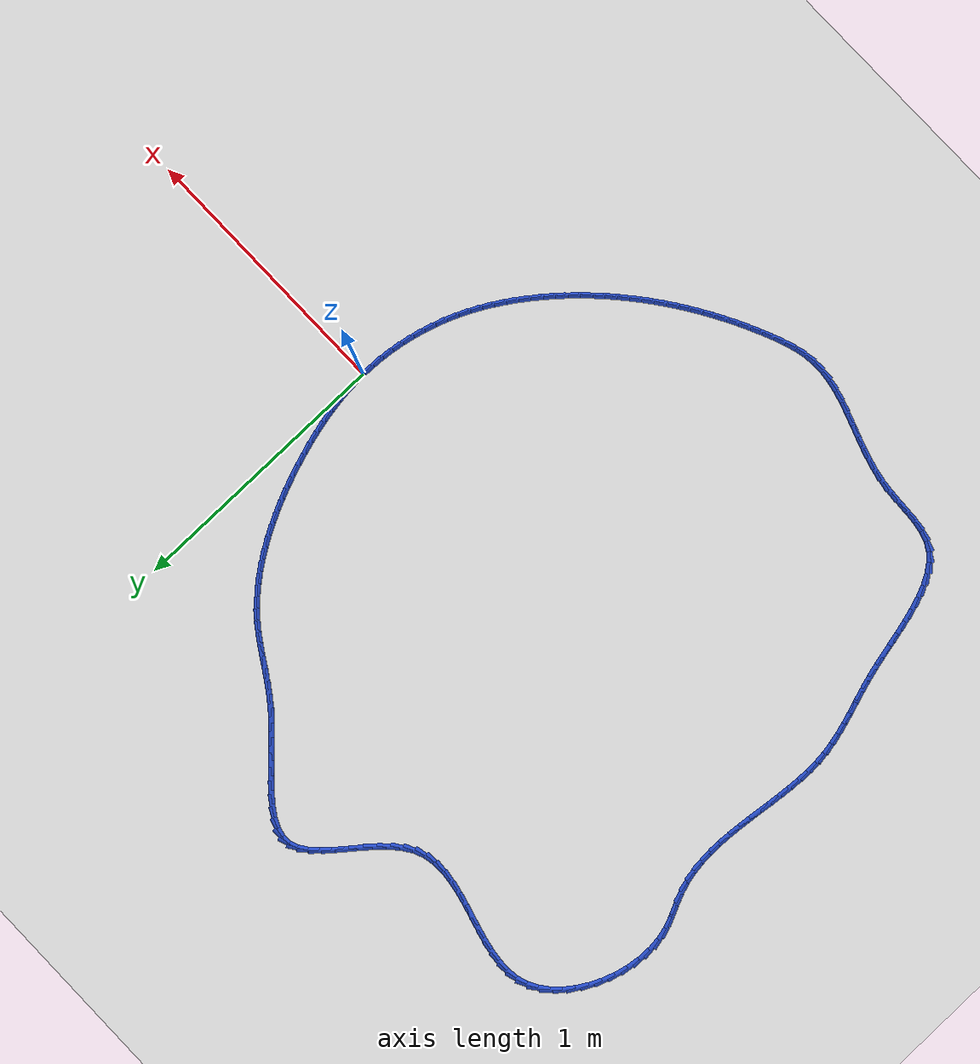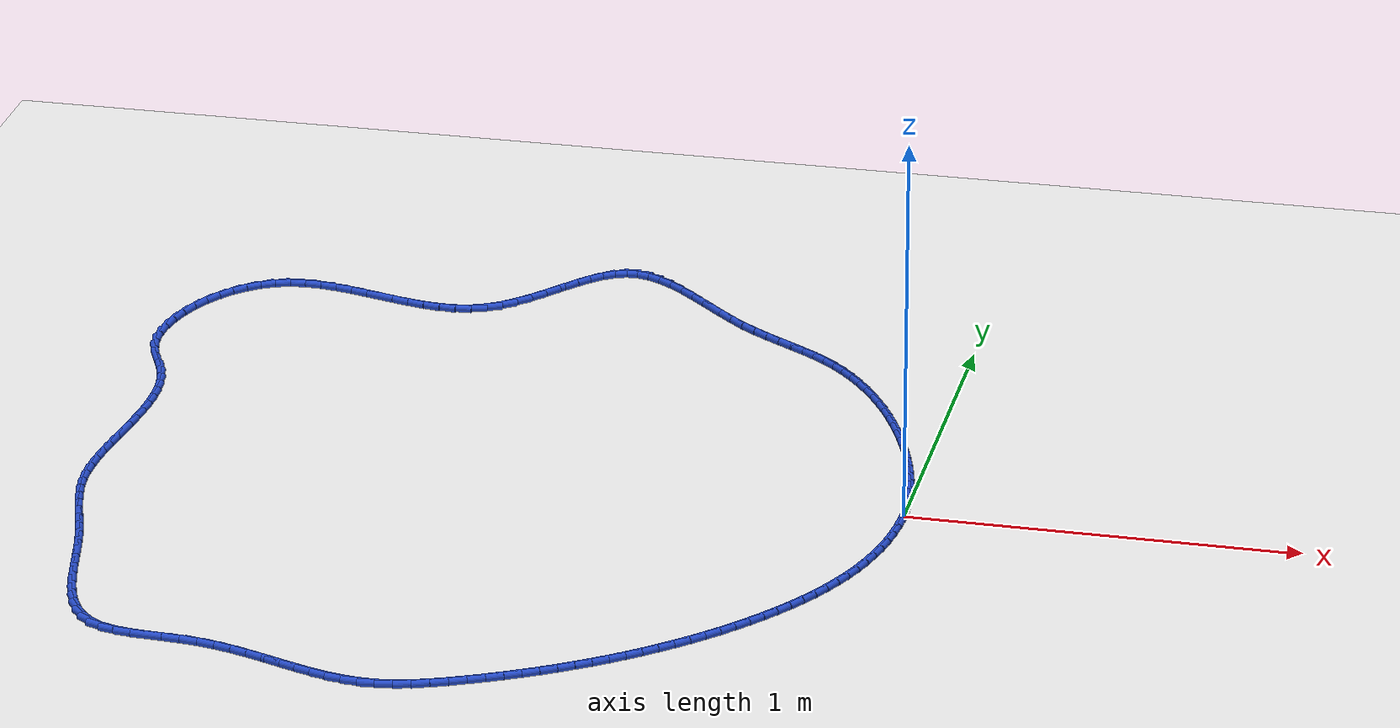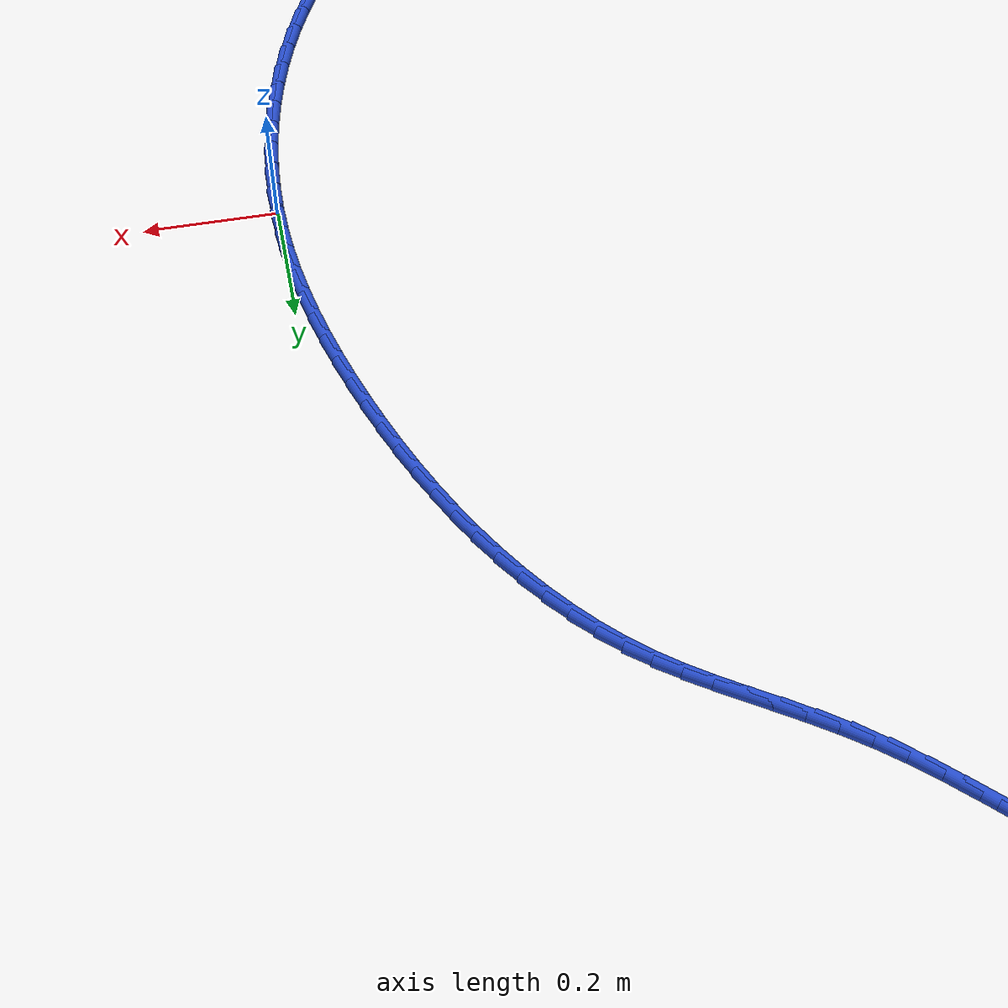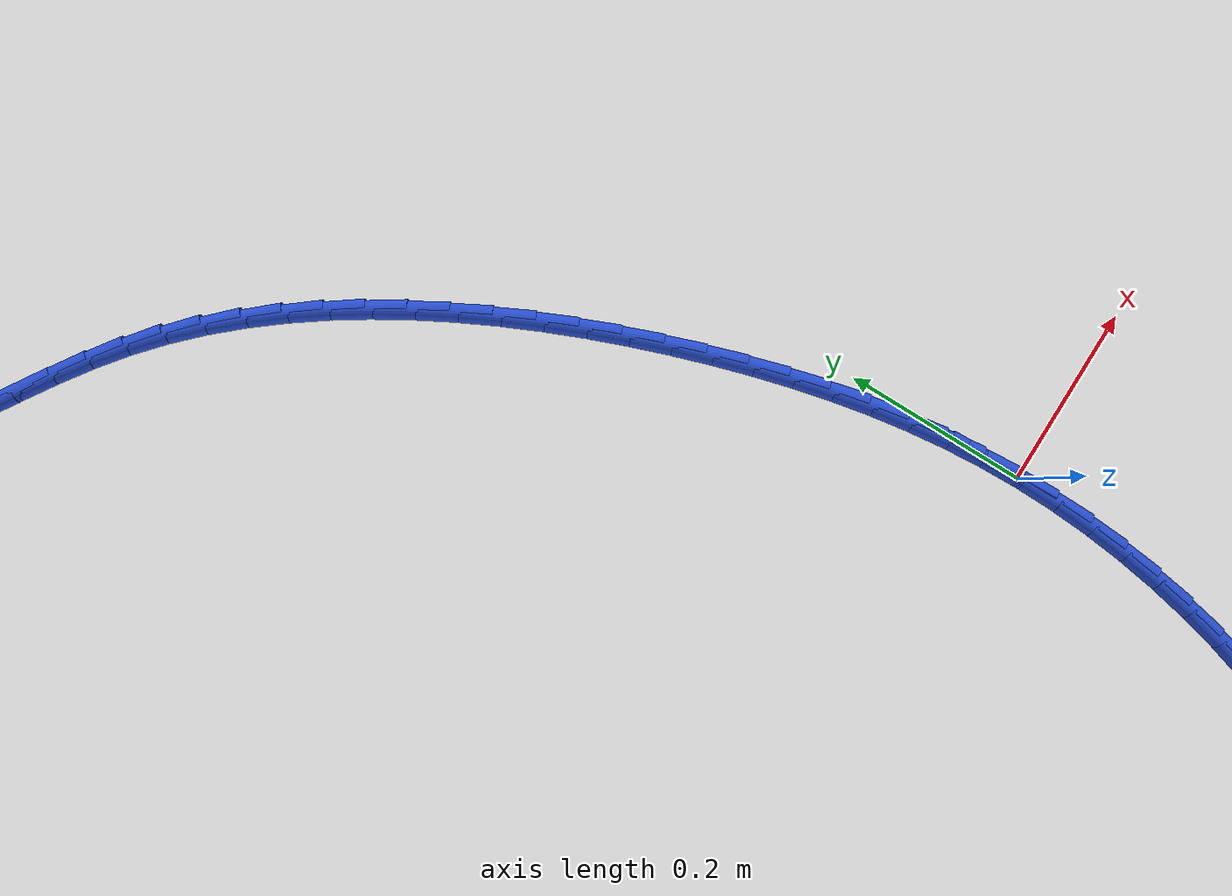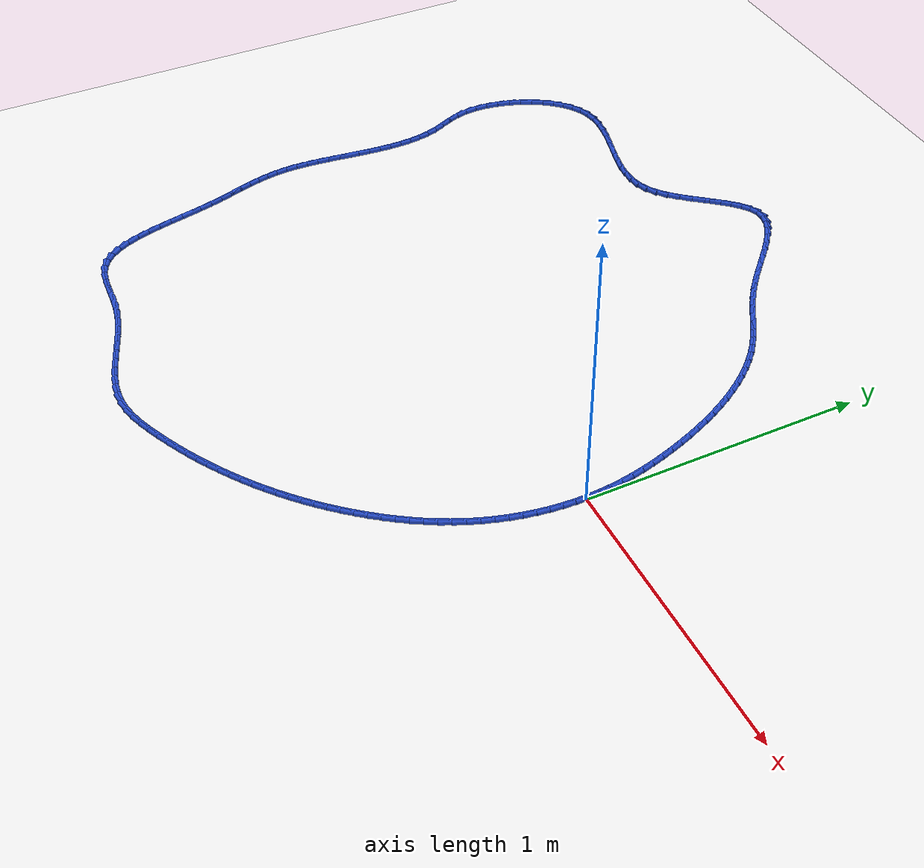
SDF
<sdf version="1.6">
 <world name="default">
  <light name="sun" type="directional">
   <pose>0 0 10 0 -0 0</pose>
   <diffuse>0.8 0.8 0.8 1</diffuse>
   <specular>0.2 0.2 0.2 1</specular>
   <attenuation>
    <range>1000</range>
    <constant>0.9</constant>
    <linear>0.01</linear>
    <quadratic>0.001</quadratic>
   </attenuation>
   <direction>-0.5 0.1 -0.9</direction>
  </light>
  <model name="ground_plane">
   <static>1</static>
   <link name="link">
    <collision name="collision">
     <geometry><plane><normal>0 0 1</normal><size>100 100</size></plane></geometry>
     <surface><friction><ode><mu>100</mu><mu2>50</mu2></ode></friction></surface>
    </collision>
    <visual name="visual">
     <cast_shadows>0</cast_shadows>
     <geometry><plane><normal>0 0 1</normal><size>100 100</size></plane></geometry>
     <material>
      <script><uri>file://media/materials/scripts/gazebo.material</uri><name>Gazebo/WhiteGlow</name></script>
     </material>
    </visual>
   </link>
  </model>
  <gravity>0 0 -9.8</gravity>
  <magnetic_field>6e-06 2.3e-05 -4.2e-05</magnetic_field>
  <atmosphere type="adiabatic"/>
  <physics name="default_physics" default="0" type="ode">
   <max_step_size>0.001</max_step_size>
   <real_time_factor>1</real_time_factor>
   <real_time_update_rate>1000</real_time_update_rate>
  </physics>
  <scene><ambient>0.4 0.4 0.4 1</ambient><background>0.7 0.7 0.7 1</background><shadows>1</shadows></scene>
  <spherical_coordinates>
   <surface_model>EARTH_WGS84</surface_model>
   <latitude_deg>0</latitude_deg>
   <longitude_deg>0</longitude_deg>
   <elevation>0</elevation>
   <heading_deg>0</heading_deg>
  </spherical_coordinates>
  <model name="line">
   <link name="link_0">
    <pose>1.9081958235744878e-17 3.469446951953614e-17 0.01 0 1.57 -1.5356192879876405</pose>
    <collision name="collision">
     <geometry><cylinder><radius>0.01</radius><length>0.08</length></cylinder></geometry>
    </collision>
    <visual name="visual">
     <material>
      <script><name>Gazebo/Blue</name><uri>file://media/materials/scripts/gazebo.material</uri></script>
     </material>
     <geometry><cylinder><radius>0.01</radius><length>0.08</length></cylinder></geometry>
    </visual>
   </link>
   <link name="link_1">
    <pose>-0.0015125934707215336 0.04298171659682079 0.01 0 1.57 -1.4902976471533067</pose>
    <collision name="collision">
     <geometry><cylinder><radius>0.01</radius><length>0.08</length></cylinder></geometry>
    </collision>
    <visual name="visual">
     <material>
      <script><name>Gazebo/Blue</name><uri>file://media/materials/scripts/gazebo.material</uri></script>
     </material>
     <geometry><cylinder><radius>0.01</radius><length>0.08</length></cylinder></geometry>
    </visual>
   </link>
   <link name="link_2">
    <pose>-0.004964846643546085 0.08577487860705432 0.01 0 1.57 -1.4473894395793307</pose>
    <collision name="collision">
     <geometry><cylinder><radius>0.01</radius><length>0.08</length></cylinder></geometry>
    </collision>
    <visual name="visual">
     <material>
      <script><name>Gazebo/Blue</name><uri>file://media/materials/scripts/gazebo.material</uri></script>
     </material>
     <geometry><cylinder><radius>0.01</radius><length>0.08</length></cylinder></geometry>
    </visual>
   </link>
   <link name="link_3">
    <pose>-0.0102526416312219 0.12840559999993736 0.01 0 1.57 -1.4070946029793014</pose>
    <collision name="collision">
     <geometry><cylinder><radius>0.01</radius><length>0.08</length></cylinder></geometry>
    </collision>
    <visual name="visual">
     <material>
      <script><name>Gazebo/Blue</name><uri>file://media/materials/scripts/gazebo.material</uri></script>
     </material>
     <geometry><cylinder><radius>0.01</radius><length>0.08</length></cylinder></geometry>
    </visual>
   </link>
   <link name="link_4">
    <pose>-0.017271860546497257 0.17089999474470668 0.01 0 1.57 -1.3695541495761743</pose>
    <collision name="collision">
     <geometry><cylinder><radius>0.01</radius><length>0.08</length></cylinder></geometry>
    </collision>
    <visual name="visual">
     <material>
      <script><name>Gazebo/Blue</name><uri>file://media/materials/scripts/gazebo.material</uri></script>
     </material>
     <geometry><cylinder><radius>0.01</radius><length>0.08</length></cylinder></geometry>
    </visual>
   </link>
   <link name="link_5">
    <pose>-0.025918385502120462 0.21328417681059914 0.01 0 1.57 -1.3348558883137478</pose>
    <collision name="collision">
     <geometry><cylinder><radius>0.01</radius><length>0.08</length></cylinder></geometry>
    </collision>
    <visual name="visual">
     <material>
      <script><name>Gazebo/Blue</name><uri>file://media/materials/scripts/gazebo.material</uri></script>
     </material>
     <geometry><cylinder><radius>0.01</radius><length>0.08</length></cylinder></geometry>
    </visual>
   </link>
   <link name="link_6">
    <pose>-0.03608809861083975 0.2555842601668513 0.01 0 1.57 -1.3030419218441027</pose>
    <collision name="collision">
     <geometry><cylinder><radius>0.01</radius><length>0.08</length></cylinder></geometry>
    </collision>
    <visual name="visual">
     <material>
      <script><name>Gazebo/Blue</name><uri>file://media/materials/scripts/gazebo.material</uri></script>
     </material>
     <geometry><cylinder><radius>0.01</radius><length>0.08</length></cylinder></geometry>
    </visual>
   </link>
   <link name="link_7">
    <pose>-0.04767688198540343 0.2978263587827001 0.01 0 1.57 -1.2741169158119359</pose>
    <collision name="collision">
     <geometry><cylinder><radius>0.01</radius><length>0.08</length></cylinder></geometry>
    </collision>
    <visual name="visual">
     <material>
      <script><name>Gazebo/Blue</name><uri>file://media/materials/scripts/gazebo.material</uri></script>
     </material>
     <geometry><cylinder><radius>0.01</radius><length>0.08</length></cylinder></geometry>
    </visual>
   </link>
   <link name="link_8">
    <pose>-0.060580617738559744 0.3400365866273821 0.01 0 1.57 -1.247971181726745</pose>
    <collision name="collision">
     <geometry><cylinder><radius>0.01</radius><length>0.08</length></cylinder></geometry>
    </collision>
    <visual name="visual">
     <material>
      <script><name>Gazebo/Blue</name><uri>file://media/materials/scripts/gazebo.material</uri></script>
     </material>
     <geometry><cylinder><radius>0.01</radius><length>0.08</length></cylinder></geometry>
    </visual>
   </link>
   <link name="link_9">
    <pose>-0.07469778131437152 0.382236863054176 0.01 0 1.57 -1.2225498965671509</pose>
    <collision name="collision">
     <geometry><cylinder><radius>0.01</radius><length>0.08</length></cylinder></geometry>
    </collision>
    <visual name="visual">
     <material>
      <script><name>Gazebo/Blue</name><uri>file://media/materials/scripts/gazebo.material</uri></script>
     </material>
     <geometry><cylinder><radius>0.01</radius><length>0.08</length></cylinder></geometry>
    </visual>
   </link>
   <link name="link_10">
    <pose>-0.0899871890345314 0.42435150831406615 0.01 0 1.57 -1.1956739762482826</pose>
    <collision name="collision">
     <geometry><cylinder><radius>0.01</radius><length>0.08</length></cylinder></geometry>
    </collision>
    <visual name="visual">
     <material>
      <script><name>Gazebo/Blue</name><uri>file://media/materials/scripts/gazebo.material</uri></script>
     </material>
     <geometry><cylinder><radius>0.01</radius><length>0.08</length></cylinder></geometry>
    </visual>
   </link>
   <link name="link_11">
    <pose>-0.10646838633580383 0.4662066155962686 0.01 0 1.57 -1.1670287262874839</pose>
    <collision name="collision">
     <geometry><cylinder><radius>0.01</radius><length>0.08</length></cylinder></geometry>
    </collision>
    <visual name="visual">
     <material>
      <script><name>Gazebo/Blue</name><uri>file://media/materials/scripts/gazebo.material</uri></script>
     </material>
     <geometry><cylinder><radius>0.01</radius><length>0.08</length></cylinder></geometry>
    </visual>
   </link>
   <link name="link_12">
    <pose>-0.1241635896347574 0.507623957880527 0.01 0 1.57 -1.1363692677235309</pose>
    <collision name="collision">
     <geometry><cylinder><radius>0.01</radius><length>0.08</length></cylinder></geometry>
    </collision>
    <visual name="visual">
     <material>
      <script><name>Gazebo/Blue</name><uri>file://media/materials/scripts/gazebo.material</uri></script>
     </material>
     <geometry><cylinder><radius>0.01</radius><length>0.08</length></cylinder></geometry>
    </visual>
   </link>
   <link name="link_13">
    <pose>-0.14309501534796065 0.5484253081465849 0.01 0 1.57 -1.1034303465614486</pose>
    <collision name="collision">
     <geometry><cylinder><radius>0.01</radius><length>0.08</length></cylinder></geometry>
    </collision>
    <visual name="visual">
     <material>
      <script><name>Gazebo/Blue</name><uri>file://media/materials/scripts/gazebo.material</uri></script>
     </material>
     <geometry><cylinder><radius>0.01</radius><length>0.08</length></cylinder></geometry>
    </visual>
   </link>
   <link name="link_14">
    <pose>-0.16328487989198204 0.5884324393741854 0.01 0 1.57 -1.0679247356543935</pose>
    <collision name="collision">
     <geometry><cylinder><radius>0.01</radius><length>0.08</length></cylinder></geometry>
    </collision>
    <visual name="visual">
     <material>
      <script><name>Gazebo/Blue</name><uri>file://media/materials/scripts/gazebo.material</uri></script>
     </material>
     <geometry><cylinder><radius>0.01</radius><length>0.08</length></cylinder></geometry>
    </visual>
   </link>
   <link name="link_15">
    <pose>-0.18475539968339025 0.6274671245430724 0.01 0 1.57 -1.0295429599865278</pose>
    <collision name="collision">
     <geometry><cylinder><radius>0.01</radius><length>0.08</length></cylinder></geometry>
    </collision>
    <visual name="visual">
     <material>
      <script><name>Gazebo/Blue</name><uri>file://media/materials/scripts/gazebo.material</uri></script>
     </material>
     <geometry><cylinder><radius>0.01</radius><length>0.08</length></cylinder></geometry>
    </visual>
   </link>
   <link name="link_16">
    <pose>-0.2075287911387538 0.6653511366329892 0.01 0 1.57 -0.9879550452614867</pose>
    <collision name="collision">
     <geometry><cylinder><radius>0.01</radius><length>0.08</length></cylinder></geometry>
    </collision>
    <visual name="visual">
     <material>
      <script><name>Gazebo/Blue</name><uri>file://media/materials/scripts/gazebo.material</uri></script>
     </material>
     <geometry><cylinder><radius>0.01</radius><length>0.08</length></cylinder></geometry>
    </visual>
   </link>
   <link name="link_17">
    <pose>-0.23162727067464117 0.7019062486236788 0.01 0 1.57 -0.9428152827927078</pose>
    <collision name="collision">
     <geometry><cylinder><radius>0.01</radius><length>0.08</length></cylinder></geometry>
    </collision>
    <visual name="visual">
     <material>
      <script><name>Gazebo/Blue</name><uri>file://media/materials/scripts/gazebo.material</uri></script>
     </material>
     <geometry><cylinder><radius>0.01</radius><length>0.08</length></cylinder></geometry>
    </visual>
   </link>
   <link name="link_18">
    <pose>-0.257073054707621 0.7369542334948853 0.01 0 1.57 -0.8937713303897217</pose>
    <collision name="collision">
     <geometry><cylinder><radius>0.01</radius><length>0.08</length></cylinder></geometry>
    </collision>
    <visual name="visual">
     <material>
      <script><name>Gazebo/Blue</name><uri>file://media/materials/scripts/gazebo.material</uri></script>
     </material>
     <geometry><cylinder><radius>0.01</radius><length>0.08</length></cylinder></geometry>
    </visual>
   </link>
   <link name="link_19">
    <pose>-0.28388835965426185 0.770316864226352 0.01 0 1.57 -0.8404792662069093</pose>
    <collision name="collision">
     <geometry><cylinder><radius>0.01</radius><length>0.08</length></cylinder></geometry>
    </collision>
    <visual name="visual">
     <material>
      <script><name>Gazebo/Blue</name><uri>file://media/materials/scripts/gazebo.material</uri></script>
     </material>
     <geometry><cylinder><radius>0.01</radius><length>0.08</length></cylinder></geometry>
    </visual>
   </link>
   <link name="link_20">
    <pose>-0.3120954019311323 0.8018159137978226 0.01 0 1.57 -0.7826263438537103</pose>
    <collision name="collision">
     <geometry><cylinder><radius>0.01</radius><length>0.08</length></cylinder></geometry>
    </collision>
    <visual name="visual">
     <material>
      <script><name>Gazebo/Blue</name><uri>file://media/materials/scripts/gazebo.material</uri></script>
     </material>
     <geometry><cylinder><radius>0.01</radius><length>0.08</length></cylinder></geometry>
    </visual>
   </link>
   <link name="link_21">
    <pose>-0.3417163979548008 0.83127315518904 0.01 0 1.57 -0.719962921207484</pose>
    <collision name="collision">
     <geometry><cylinder><radius>0.01</radius><length>0.08</length></cylinder></geometry>
    </collision>
    <visual name="visual">
     <material>
      <script><name>Gazebo/Blue</name><uri>file://media/materials/scripts/gazebo.material</uri></script>
     </material>
     <geometry><cylinder><radius>0.01</radius><length>0.08</length></cylinder></geometry>
    </visual>
   </link>
   <link name="link_22">
    <pose>-0.3727735641418358 0.8585103613797479 0.01 0 1.57 -0.6558438962309355</pose>
    <collision name="collision">
     <geometry><cylinder><radius>0.01</radius><length>0.08</length></cylinder></geometry>
    </collision>
    <visual name="visual">
     <material>
      <script><name>Gazebo/Blue</name><uri>file://media/materials/scripts/gazebo.material</uri></script>
     </material>
     <geometry><cylinder><radius>0.01</radius><length>0.08</length></cylinder></geometry>
    </visual>
   </link>
   <link name="link_23">
    <pose>-0.4052553957224594 0.8835040523797999 0.01 0 1.57 -0.6058327614477008</pose>
    <collision name="collision">
     <geometry><cylinder><radius>0.01</radius><length>0.08</length></cylinder></geometry>
    </collision>
    <visual name="visual">
     <material>
      <script><name>Gazebo/Blue</name><uri>file://media/materials/scripts/gazebo.material</uri></script>
     </material>
     <geometry><cylinder><radius>0.01</radius><length>0.08</length></cylinder></geometry>
    </visual>
   </link>
   <link name="link_24">
    <pose>-0.43900772376808944 0.9068854361643817 0.01 0 1.57 -0.575027508403918</pose>
    <collision name="collision">
     <geometry><cylinder><radius>0.01</radius><length>0.08</length></cylinder></geometry>
    </collision>
    <visual name="visual">
     <material>
      <script><name>Gazebo/Blue</name><uri>file://media/materials/scripts/gazebo.material</uri></script>
     </material>
     <geometry><cylinder><radius>0.01</radius><length>0.08</length></cylinder></geometry>
    </visual>
   </link>
   <link name="link_25">
    <pose>-0.4738386575860525 0.9294588264500868 0.01 0 1.57 -0.5635403185666521</pose>
    <collision name="collision">
     <geometry><cylinder><radius>0.01</radius><length>0.08</length></cylinder></geometry>
    </collision>
    <visual name="visual">
     <material>
      <script><name>Gazebo/Blue</name><uri>file://media/materials/scripts/gazebo.material</uri></script>
     </material>
     <geometry><cylinder><radius>0.01</radius><length>0.08</length></cylinder></geometry>
    </visual>
   </link>
   <link name="link_26">
    <pose>-0.5095563062508094 0.9520285380221327 0.01 0 1.57 -0.5706051086391455</pose>
    <collision name="collision">
     <geometry><cylinder><radius>0.01</radius><length>0.08</length></cylinder></geometry>
    </collision>
    <visual name="visual">
     <material>
      <script><name>Gazebo/Blue</name><uri>file://media/materials/scripts/gazebo.material</uri></script>
     </material>
     <geometry><cylinder><radius>0.01</radius><length>0.08</length></cylinder></geometry>
    </visual>
   </link>
   <link name="link_27">
    <pose>-0.5459687788368206 0.9753988856657364 0.01 0 1.57 -0.5948170970099868</pose>
    <collision name="collision">
     <geometry><cylinder><radius>0.01</radius><length>0.08</length></cylinder></geometry>
    </collision>
    <visual name="visual">
     <material>
      <script><name>Gazebo/Blue</name><uri>file://media/materials/scripts/gazebo.material</uri></script>
     </material>
     <geometry><cylinder><radius>0.01</radius><length>0.08</length></cylinder></geometry>
    </visual>
   </link>
   <link name="link_28">
    <pose>-0.5828841844185473 1.0003741841661153 0.01 0 1.57 -0.6342349878830041</pose>
    <collision name="collision">
     <geometry><cylinder><radius>0.01</radius><length>0.08</length></cylinder></geometry>
    </collision>
    <visual name="visual">
     <material>
      <script><name>Gazebo/Blue</name><uri>file://media/materials/scripts/gazebo.material</uri></script>
     </material>
     <geometry><cylinder><radius>0.01</radius><length>0.08</length></cylinder></geometry>
    </visual>
   </link>
   <link name="link_29">
    <pose>-0.62011063207045 1.0277587483084871 0.01 0 1.57 -0.6860929498584207</pose>
    <collision name="collision">
     <geometry><cylinder><radius>0.01</radius><length>0.08</length></cylinder></geometry>
    </collision>
    <visual name="visual">
     <material>
      <script><name>Gazebo/Blue</name><uri>file://media/materials/scripts/gazebo.material</uri></script>
     </material>
     <geometry><cylinder><radius>0.01</radius><length>0.08</length></cylinder></geometry>
    </visual>
   </link>
   <link name="link_30">
    <pose>-0.6574569744867412 1.0583375126407861 0.01 0 1.57 -0.7342811216919091</pose>
    <collision name="collision">
     <geometry><cylinder><radius>0.01</radius><length>0.08</length></cylinder></geometry>
    </collision>
    <visual name="visual">
     <material>
      <script><name>Gazebo/Blue</name><uri>file://media/materials/scripts/gazebo.material</uri></script>
     </material>
     <geometry><cylinder><radius>0.01</radius><length>0.08</length></cylinder></geometry>
    </visual>
   </link>
   <link name="link_31">
    <pose>-0.6947658596090776 1.0920146390941072 0.01 0 1.57 -0.7619201479088347</pose>
    <collision name="collision">
     <geometry><cylinder><radius>0.01</radius><length>0.08</length></cylinder></geometry>
    </collision>
    <visual name="visual">
     <material>
      <script><name>Gazebo/Blue</name><uri>file://media/materials/scripts/gazebo.material</uri></script>
     </material>
     <geometry><cylinder><radius>0.01</radius><length>0.08</length></cylinder></geometry>
    </visual>
   </link>
   <link name="link_32">
    <pose>-0.7319268937152781 1.1274704602226113 0.01 0 1.57 -0.7705261317645066</pose>
    <collision name="collision">
     <geometry><cylinder><radius>0.01</radius><length>0.08</length></cylinder></geometry>
    </collision>
    <visual name="visual">
     <material>
      <script><name>Gazebo/Blue</name><uri>file://media/materials/scripts/gazebo.material</uri></script>
     </material>
     <geometry><cylinder><radius>0.01</radius><length>0.08</length></cylinder></geometry>
    </visual>
   </link>
   <link name="link_33">
    <pose>-0.7688331489415055 1.163294981290243 0.01 0 1.57 -0.7607098235044691</pose>
    <collision name="collision">
     <geometry><cylinder><radius>0.01</radius><length>0.08</length></cylinder></geometry>
    </collision>
    <visual name="visual">
     <material>
      <script><name>Gazebo/Blue</name><uri>file://media/materials/scripts/gazebo.material</uri></script>
     </material>
     <geometry><cylinder><radius>0.01</radius><length>0.08</length></cylinder></geometry>
    </visual>
   </link>
   <link name="link_34">
    <pose>-0.8053776974239232 1.1980782075609473 0.01 0 1.57 -0.7307224854706224</pose>
    <collision name="collision">
     <geometry><cylinder><radius>0.01</radius><length>0.08</length></cylinder></geometry>
    </collision>
    <visual name="visual">
     <material>
      <script><name>Gazebo/Blue</name><uri>file://media/materials/scripts/gazebo.material</uri></script>
     </material>
     <geometry><cylinder><radius>0.01</radius><length>0.08</length></cylinder></geometry>
    </visual>
   </link>
   <link name="link_35">
    <pose>-0.8414536112986943 1.2304101442986695 0.01 0 1.57 -0.6759484763236466</pose>
    <collision name="collision">
     <geometry><cylinder><radius>0.01</radius><length>0.08</length></cylinder></geometry>
    </collision>
    <visual name="visual">
     <material>
      <script><name>Gazebo/Blue</name><uri>file://media/materials/scripts/gazebo.material</uri></script>
     </material>
     <geometry><cylinder><radius>0.01</radius><length>0.08</length></cylinder></geometry>
    </visual>
   </link>
   <link name="link_36">
    <pose>-0.8769539627019824 1.2588807967673548 0.01 0 1.57 -0.5877533416081191</pose>
    <collision name="collision">
     <geometry><cylinder><radius>0.01</radius><length>0.08</length></cylinder></geometry>
    </collision>
    <visual name="visual">
     <material>
      <script><name>Gazebo/Blue</name><uri>file://media/materials/scripts/gazebo.material</uri></script>
     </material>
     <geometry><cylinder><radius>0.01</radius><length>0.08</length></cylinder></geometry>
    </visual>
   </link>
   <link name="link_37">
    <pose>-0.9117718237699506 1.2820801702309477 0.01 0 1.57 -0.45191603260949115</pose>
    <collision name="collision">
     <geometry><cylinder><radius>0.01</radius><length>0.08</length></cylinder></geometry>
    </collision>
    <visual name="visual">
     <material>
      <script><name>Gazebo/Blue</name><uri>file://media/materials/scripts/gazebo.material</uri></script>
     </material>
     <geometry><cylinder><radius>0.01</radius><length>0.08</length></cylinder></geometry>
    </visual>
   </link>
   <link name="link_38">
    <pose>-0.9458002666387614 1.2985982699533933 0.01 0 1.57 -0.24905956902135706</pose>
    <collision name="collision">
     <geometry><cylinder><radius>0.01</radius><length>0.08</length></cylinder></geometry>
    </collision>
    <visual name="visual">
     <material>
      <script><name>Gazebo/Blue</name><uri>file://media/materials/scripts/gazebo.material</uri></script>
     </material>
     <geometry><cylinder><radius>0.01</radius><length>0.08</length></cylinder></geometry>
    </visual>
   </link>
   <link name="link_39">
    <pose>-0.978932363444579 1.3070251011986365 0.01 0 1.57 0.03342891580712591</pose>
    <collision name="collision">
     <geometry><cylinder><radius>0.01</radius><length>0.08</length></cylinder></geometry>
    </collision>
    <visual name="visual">
     <material>
      <script><name>Gazebo/Blue</name><uri>file://media/materials/scripts/gazebo.material</uri></script>
     </material>
     <geometry><cylinder><radius>0.01</radius><length>0.08</length></cylinder></geometry>
    </visual>
   </link>
   <link name="link_40">
    <pose>-1.0110611863235661 1.3059506692306226 0.01 0 1.57 0.3555052589625959</pose>
    <collision name="collision">
     <geometry><cylinder><radius>0.01</radius><length>0.08</length></cylinder></geometry>
    </collision>
    <visual name="visual">
     <material>
      <script><name>Gazebo/Blue</name><uri>file://media/materials/scripts/gazebo.material</uri></script>
     </material>
     <geometry><cylinder><radius>0.01</radius><length>0.08</length></cylinder></geometry>
    </visual>
   </link>
   <link name="link_41">
    <pose>-1.0421387808163007 1.294412182050188 0.01 0 1.57 0.6007287738151522</pose>
    <collision name="collision">
     <geometry><cylinder><radius>0.01</radius><length>0.08</length></cylinder></geometry>
    </collision>
    <visual name="visual">
     <material>
      <script><name>Gazebo/Blue</name><uri>file://media/materials/scripts/gazebo.material</uri></script>
     </material>
     <geometry><cylinder><radius>0.01</radius><length>0.08</length></cylinder></geometry>
    </visual>
   </link>
   <link name="link_42">
    <pose>-1.0724103483524634 1.2736698856062618 0.01 0 1.57 0.7541746495810016</pose>
    <collision name="collision">
     <geometry><cylinder><radius>0.01</radius><length>0.08</length></cylinder></geometry>
    </collision>
    <visual name="visual">
     <material>
      <script><name>Gazebo/Blue</name><uri>file://media/materials/scripts/gazebo.material</uri></script>
     </material>
     <geometry><cylinder><radius>0.01</radius><length>0.08</length></cylinder></geometry>
    </visual>
   </link>
   <link name="link_43">
    <pose>-1.1022120086891347 1.2456734709501964 0.01 0 1.57 0.8430254866480653</pose>
    <collision name="collision">
     <geometry><cylinder><radius>0.01</radius><length>0.08</length></cylinder></geometry>
    </collision>
    <visual name="visual">
     <material>
      <script><name>Gazebo/Blue</name><uri>file://media/materials/scripts/gazebo.material</uri></script>
     </material>
     <geometry><cylinder><radius>0.01</radius><length>0.08</length></cylinder></geometry>
    </visual>
   </link>
   <link name="link_44">
    <pose>-1.131879909403983 1.2123728401003533 0.01 0 1.57 0.8870329697762767</pose>
    <collision name="collision">
     <geometry><cylinder><radius>0.01</radius><length>0.08</length></cylinder></geometry>
    </collision>
    <visual name="visual">
     <material>
      <script><name>Gazebo/Blue</name><uri>file://media/materials/scripts/gazebo.material</uri></script>
     </material>
     <geometry><cylinder><radius>0.01</radius><length>0.08</length></cylinder></geometry>
    </visual>
   </link>
   <link name="link_45">
    <pose>-1.1617501980746763 1.175717895075094 0.01 0 1.57 0.8966750953807631</pose>
    <collision name="collision">
     <geometry><cylinder><radius>0.01</radius><length>0.08</length></cylinder></geometry>
    </collision>
    <visual name="visual">
     <material>
      <script><name>Gazebo/Blue</name><uri>file://media/materials/scripts/gazebo.material</uri></script>
     </material>
     <geometry><cylinder><radius>0.01</radius><length>0.08</length></cylinder></geometry>
    </visual>
   </link>
   <link name="link_46">
    <pose>-1.192159022278882 1.1376585378927824 0.01 0 1.57 0.8757128159286771</pose>
    <collision name="collision">
     <geometry><cylinder><radius>0.01</radius><length>0.08</length></cylinder></geometry>
    </collision>
    <visual name="visual">
     <material>
      <script><name>Gazebo/Blue</name><uri>file://media/materials/scripts/gazebo.material</uri></script>
     </material>
     <geometry><cylinder><radius>0.01</radius><length>0.08</length></cylinder></geometry>
    </visual>
   </link>
   <link name="link_47">
    <pose>-1.2234425295942688 1.1001446705717783 0.01 0 1.57 0.8227682890199755</pose>
    <collision name="collision">
     <geometry><cylinder><radius>0.01</radius><length>0.08</length></cylinder></geometry>
    </collision>
    <visual name="visual">
     <material>
      <script><name>Gazebo/Blue</name><uri>file://media/materials/scripts/gazebo.material</uri></script>
     </material>
     <geometry><cylinder><radius>0.01</radius><length>0.08</length></cylinder></geometry>
    </visual>
   </link>
   <link name="link_48">
    <pose>-1.2559368675985043 1.0651261951304458 0.01 0 1.57 0.7317753680354135</pose>
    <collision name="collision">
     <geometry><cylinder><radius>0.01</radius><length>0.08</length></cylinder></geometry>
    </collision>
    <visual name="visual">
     <material>
      <script><name>Gazebo/Blue</name><uri>file://media/materials/scripts/gazebo.material</uri></script>
     </material>
     <geometry><cylinder><radius>0.01</radius><length>0.08</length></cylinder></geometry>
    </visual>
   </link>
   <link name="link_49">
    <pose>-1.2899781838692568 1.0345530135871464 0.01 0 1.57 0.5923904299504142</pose>
    <collision name="collision">
     <geometry><cylinder><radius>0.01</radius><length>0.08</length></cylinder></geometry>
    </collision>
    <visual name="visual">
     <material>
      <script><name>Gazebo/Blue</name><uri>file://media/materials/scripts/gazebo.material</uri></script>
     </material>
     <geometry><cylinder><radius>0.01</radius><length>0.08</length></cylinder></geometry>
    </visual>
   </link>
   <link name="link_50">
    <pose>-1.3259026259841944 1.0103750279602415 0.01 0 1.57 0.39872541099691333</pose>
    <collision name="collision">
     <geometry><cylinder><radius>0.01</radius><length>0.08</length></cylinder></geometry>
    </collision>
    <visual name="visual">
     <material>
      <script><name>Gazebo/Blue</name><uri>file://media/materials/scripts/gazebo.material</uri></script>
     </material>
     <geometry><cylinder><radius>0.01</radius><length>0.08</length></cylinder></geometry>
    </visual>
   </link>
   <link name="link_51">
    <pose>-1.364001196661025 0.9943244201579707 0.01 0 1.57 0.20021233508018516</pose>
    <collision name="collision">
     <geometry><cylinder><radius>0.01</radius><length>0.08</length></cylinder></geometry>
    </collision>
    <visual name="visual">
     <material>
      <script><name>Gazebo/Blue</name><uri>file://media/materials/scripts/gazebo.material</uri></script>
     </material>
     <geometry><cylinder><radius>0.01</radius><length>0.08</length></cylinder></geometry>
    </visual>
   </link>
   <link name="link_52">
    <pose>-1.4041588622783958 0.9861751806902 0.01 0 1.57 0.036023812036118166</pose>
    <collision name="collision">
     <geometry><cylinder><radius>0.01</radius><length>0.08</length></cylinder></geometry>
    </collision>
    <visual name="visual">
     <material>
      <script><name>Gazebo/Blue</name><uri>file://media/materials/scripts/gazebo.material</uri></script>
     </material>
     <geometry><cylinder><radius>0.01</radius><length>0.08</length></cylinder></geometry>
    </visual>
   </link>
   <link name="link_53">
    <pose>-1.4460458338179052 0.9846655992420176 0.01 0 1.57 -0.0889180719076776</pose>
    <collision name="collision">
     <geometry><cylinder><radius>0.01</radius><length>0.08</length></cylinder></geometry>
    </collision>
    <visual name="visual">
     <material>
      <script><name>Gazebo/Blue</name><uri>file://media/materials/scripts/gazebo.material</uri></script>
     </material>
     <geometry><cylinder><radius>0.01</radius><length>0.08</length></cylinder></geometry>
    </visual>
   </link>
   <link name="link_54">
    <pose>-1.489330370412135 0.9885245523165193 0.01 0 1.57 -0.17750972775380994</pose>
    <collision name="collision">
     <geometry><cylinder><radius>0.01</radius><length>0.08</length></cylinder></geometry>
    </collision>
    <visual name="visual">
     <material>
      <script><name>Gazebo/Blue</name><uri>file://media/materials/scripts/gazebo.material</uri></script>
     </material>
     <geometry><cylinder><radius>0.01</radius><length>0.08</length></cylinder></geometry>
    </visual>
   </link>
   <link name="link_55">
    <pose>-1.533680731193668 0.9964809164168013 0.01 0 1.57 -0.23475594887704712</pose>
    <collision name="collision">
     <geometry><cylinder><radius>0.01</radius><length>0.08</length></cylinder></geometry>
    </collision>
    <visual name="visual">
     <material>
      <script><name>Gazebo/Blue</name><uri>file://media/materials/scripts/gazebo.material</uri></script>
     </material>
     <geometry><cylinder><radius>0.01</radius><length>0.08</length></cylinder></geometry>
    </visual>
   </link>
   <link name="link_56">
    <pose>-1.5787651752950846 1.0072635680459594 0.01 0 1.57 -0.26486680333086177</pose>
    <collision name="collision">
     <geometry><cylinder><radius>0.01</radius><length>0.08</length></cylinder></geometry>
    </collision>
    <visual name="visual">
     <material>
      <script><name>Gazebo/Blue</name><uri>file://media/materials/scripts/gazebo.material</uri></script>
     </material>
     <geometry><cylinder><radius>0.01</radius><length>0.08</length></cylinder></geometry>
    </visual>
   </link>
   <link name="link_57">
    <pose>-1.624251961848968 1.0196013837070896 0.01 0 1.57 -0.2702747852639967</pose>
    <collision name="collision">
     <geometry><cylinder><radius>0.01</radius><length>0.08</length></cylinder></geometry>
    </collision>
    <visual name="visual">
     <material>
      <script><name>Gazebo/Blue</name><uri>file://media/materials/scripts/gazebo.material</uri></script>
     </material>
     <geometry><cylinder><radius>0.01</radius><length>0.08</length></cylinder></geometry>
    </visual>
   </link>
   <link name="link_58">
    <pose>-1.6698093499879 1.0322232399032885 0.01 0 1.57 -0.2514241996928609</pose>
    <collision name="collision">
     <geometry><cylinder><radius>0.01</radius><length>0.08</length></cylinder></geometry>
    </collision>
    <visual name="visual">
     <material>
      <script><name>Gazebo/Blue</name><uri>file://media/materials/scripts/gazebo.material</uri></script>
     </material>
     <geometry><cylinder><radius>0.01</radius><length>0.08</length></cylinder></geometry>
    </visual>
   </link>
   <link name="link_59">
    <pose>-1.715105598844462 1.0438580131376518 0.01 0 1.57 -0.20675349552007033</pose>
    <collision name="collision">
     <geometry><cylinder><radius>0.01</radius><length>0.08</length></cylinder></geometry>
    </collision>
    <visual name="visual">
     <material>
      <script><name>Gazebo/Blue</name><uri>file://media/materials/scripts/gazebo.material</uri></script>
     </material>
     <geometry><cylinder><radius>0.01</radius><length>0.08</length></cylinder></geometry>
    </visual>
   </link>
   <link name="link_60">
    <pose>-1.7598089675512354 1.0532345799132754 0.01 0 1.57 -0.13277753829971048</pose>
    <collision name="collision">
     <geometry><cylinder><radius>0.01</radius><length>0.08</length></cylinder></geometry>
    </collision>
    <visual name="visual">
     <material>
      <script><name>Gazebo/Blue</name><uri>file://media/materials/scripts/gazebo.material</uri></script>
     </material>
     <geometry><cylinder><radius>0.01</radius><length>0.08</length></cylinder></geometry>
    </visual>
   </link>
   <link name="link_61">
    <pose>-1.8035877152408042 1.0590818167332556 0.01 0 1.57 -0.02461225943537822</pose>
    <collision name="collision">
     <geometry><cylinder><radius>0.01</radius><length>0.08</length></cylinder></geometry>
    </collision>
    <visual name="visual">
     <material>
      <script><name>Gazebo/Blue</name><uri>file://media/materials/scripts/gazebo.material</uri></script>
     </material>
     <geometry><cylinder><radius>0.01</radius><length>0.08</length></cylinder></geometry>
    </visual>
   </link>
   <link name="link_62">
    <pose>-1.8461101010457486 1.0601286001006887 0.01 0 1.57 0.12214165535891941</pose>
    <collision name="collision">
     <geometry><cylinder><radius>0.01</radius><length>0.08</length></cylinder></geometry>
    </collision>
    <visual name="visual">
     <material>
      <script><name>Gazebo/Blue</name><uri>file://media/materials/scripts/gazebo.material</uri></script>
     </material>
     <geometry><cylinder><radius>0.01</radius><length>0.08</length></cylinder></geometry>
    </visual>
   </link>
   <link name="link_63">
    <pose>-1.887044384098651 1.05510380651867 0.01 0 1.57 0.3065289898121416</pose>
    <collision name="collision">
     <geometry><cylinder><radius>0.01</radius><length>0.08</length></cylinder></geometry>
    </collision>
    <visual name="visual">
     <material>
      <script><name>Gazebo/Blue</name><uri>file://media/materials/scripts/gazebo.material</uri></script>
     </material>
     <geometry><cylinder><radius>0.01</radius><length>0.08</length></cylinder></geometry>
    </visual>
   </link>
   <link name="link_64">
    <pose>-1.9260586694177841 1.0427556068904404 0.01 0 1.57 0.49922334966378734</pose>
    <collision name="collision">
     <geometry><cylinder><radius>0.01</radius><length>0.08</length></cylinder></geometry>
    </collision>
    <visual name="visual">
     <material>
      <script><name>Gazebo/Blue</name><uri>file://media/materials/scripts/gazebo.material</uri></script>
     </material>
     <geometry><cylinder><radius>0.01</radius><length>0.08</length></cylinder></geometry>
    </visual>
   </link>
   <link name="link_65">
    <pose>-1.962814025483637 1.0227131141729793 0.01 0 1.57 0.6668903602043066</pose>
    <collision name="collision">
     <geometry><cylinder><radius>0.01</radius><length>0.08</length></cylinder></geometry>
    </collision>
    <visual name="visual">
     <material>
      <script><name>Gazebo/Blue</name><uri>file://media/materials/scripts/gazebo.material</uri></script>
     </material>
     <geometry><cylinder><radius>0.01</radius><length>0.08</length></cylinder></geometry>
    </visual>
   </link>
   <link name="link_66">
    <pose>-1.9969617246605496 0.9958318698512343 0.01 0 1.57 0.8101427581042655</pose>
    <collision name="collision">
     <geometry><cylinder><radius>0.01</radius><length>0.08</length></cylinder></geometry>
    </collision>
    <visual name="visual">
     <material>
      <script><name>Gazebo/Blue</name><uri>file://media/materials/scripts/gazebo.material</uri></script>
     </material>
     <geometry><cylinder><radius>0.01</radius><length>0.08</length></cylinder></geometry>
    </visual>
   </link>
   <link name="link_67">
    <pose>-2.0281523142724387 0.9630581871247775 0.01 0 1.57 0.9342166323017278</pose>
    <collision name="collision">
     <geometry><cylinder><radius>0.01</radius><length>0.08</length></cylinder></geometry>
    </collision>
    <visual name="visual">
     <material>
      <script><name>Gazebo/Blue</name><uri>file://media/materials/scripts/gazebo.material</uri></script>
     </material>
     <geometry><cylinder><radius>0.01</radius><length>0.08</length></cylinder></geometry>
    </visual>
   </link>
   <link name="link_68">
    <pose>-2.0560363416432206 0.9253383791931806 0.01 0 1.57 1.0446632798559419</pose>
    <collision name="collision">
     <geometry><cylinder><radius>0.01</radius><length>0.08</length></cylinder></geometry>
    </collision>
    <visual name="visual">
     <material>
      <script><name>Gazebo/Blue</name><uri>file://media/materials/scripts/gazebo.material</uri></script>
     </material>
     <geometry><cylinder><radius>0.01</radius><length>0.08</length></cylinder></geometry>
    </visual>
   </link>
   <link name="link_69">
    <pose>-2.080264354096813 0.8836187592560159 0.01 0 1.57 1.146556901200994</pose>
    <collision name="collision">
     <geometry><cylinder><radius>0.01</radius><length>0.08</length></cylinder></geometry>
    </collision>
    <visual name="visual">
     <material>
      <script><name>Gazebo/Blue</name><uri>file://media/materials/scripts/gazebo.material</uri></script>
     </material>
     <geometry><cylinder><radius>0.01</radius><length>0.08</length></cylinder></geometry>
    </visual>
   </link>
   <link name="link_70">
    <pose>-2.100486898957132 0.8388456405128546 0.01 0 1.57 1.2444290000455371</pose>
    <collision name="collision">
     <geometry><cylinder><radius>0.01</radius><length>0.08</length></cylinder></geometry>
    </collision>
    <visual name="visual">
     <material>
      <script><name>Gazebo/Blue</name><uri>file://media/materials/scripts/gazebo.material</uri></script>
     </material>
     <geometry><cylinder><radius>0.01</radius><length>0.08</length></cylinder></geometry>
    </visual>
   </link>
   <link name="link_71">
    <pose>-2.116354523548095 0.7919653361632684 0.01 0 1.57 1.3424796940436667</pose>
    <collision name="collision">
     <geometry><cylinder><radius>0.01</radius><length>0.08</length></cylinder></geometry>
    </collision>
    <visual name="visual">
     <material>
      <script><name>Gazebo/Blue</name><uri>file://media/materials/scripts/gazebo.material</uri></script>
     </material>
     <geometry><cylinder><radius>0.01</radius><length>0.08</length></cylinder></geometry>
    </visual>
   </link>
   <link name="link_72">
    <pose>-2.1275177751936183 0.7439241594068297 0.01 0 1.57 1.4448611631395563</pose>
    <collision name="collision">
     <geometry><cylinder><radius>0.01</radius><length>0.08</length></cylinder></geometry>
    </collision>
    <visual name="visual">
     <material>
      <script><name>Gazebo/Blue</name><uri>file://media/materials/scripts/gazebo.material</uri></script>
     </material>
     <geometry><cylinder><radius>0.01</radius><length>0.08</length></cylinder></geometry>
    </visual>
   </link>
   <link name="link_73">
    <pose>-2.133627201217619 0.6956684234431101 0.01 0 1.57 1.5559386541939455</pose>
    <collision name="collision">
     <geometry><cylinder><radius>0.01</radius><length>0.08</length></cylinder></geometry>
    </collision>
    <visual name="visual">
     <material>
      <script><name>Gazebo/Blue</name><uri>file://media/materials/scripts/gazebo.material</uri></script>
     </material>
     <geometry><cylinder><radius>0.01</radius><length>0.08</length></cylinder></geometry>
    </visual>
   </link>
   <link name="link_74">
    <pose>-2.134333348944015 0.648144441471681 0.01 0 1.57 -1.4611606676408353</pose>
    <collision name="collision">
     <geometry><cylinder><radius>0.01</radius><length>0.08</length></cylinder></geometry>
    </collision>
    <visual name="visual">
     <material>
      <script><name>Gazebo/Blue</name><uri>file://media/materials/scripts/gazebo.material</uri></script>
     </material>
     <geometry><cylinder><radius>0.01</radius><length>0.08</length></cylinder></geometry>
    </visual>
   </link>
   <link name="link_75">
    <pose>-2.1292867656967216 0.6022985266921151 0.01 0 1.57 -1.319274555083969</pose>
    <collision name="collision">
     <geometry><cylinder><radius>0.01</radius><length>0.08</length></cylinder></geometry>
    </collision>
    <visual name="visual">
     <material>
      <script><name>Gazebo/Blue</name><uri>file://media/materials/scripts/gazebo.material</uri></script>
     </material>
     <geometry><cylinder><radius>0.01</radius><length>0.08</length></cylinder></geometry>
    </visual>
   </link>
   <link name="link_76">
    <pose>-2.118174416231469 0.5590536782854657 0.01 0 1.57 -1.1944401174038335</pose>
    <collision name="collision">
     <geometry><cylinder><radius>0.01</radius><length>0.08</length></cylinder></geometry>
    </collision>
    <visual name="visual">
     <material>
      <script><name>Gazebo/Blue</name><uri>file://media/materials/scripts/gazebo.material</uri></script>
     </material>
     <geometry><cylinder><radius>0.01</radius><length>0.08</length></cylinder></geometry>
    </visual>
   </link>
   <link name="link_77">
    <pose>-2.102114827737014 0.5184164257255275 0.01 0 1.57 -1.140111327923376</pose>
    <collision name="collision">
     <geometry><cylinder><radius>0.01</radius><length>0.08</length></cylinder></geometry>
    </collision>
    <visual name="visual">
     <material>
      <script><name>Gazebo/Blue</name><uri>file://media/materials/scripts/gazebo.material</uri></script>
     </material>
     <geometry><cylinder><radius>0.01</radius><length>0.08</length></cylinder></geometry>
    </visual>
   </link>
   <link name="link_78">
    <pose>-2.0840953905109982 0.4791968739454712 0.01 0 1.57 -1.1632956525139542</pose>
    <collision name="collision">
     <geometry><cylinder><radius>0.01</radius><length>0.08</length></cylinder></geometry>
    </collision>
    <visual name="visual">
     <material>
      <script><name>Gazebo/Blue</name><uri>file://media/materials/scripts/gazebo.material</uri></script>
     </material>
     <geometry><cylinder><radius>0.01</radius><length>0.08</length></cylinder></geometry>
    </visual>
   </link>
   <link name="link_79">
    <pose>-2.0672293251807052 0.4401245727572146 0.01 0 1.57 -1.2536866452528141</pose>
    <collision name="collision">
     <geometry><cylinder><radius>0.01</radius><length>0.08</length></cylinder></geometry>
    </collision>
    <visual name="visual">
     <material>
      <script><name>Gazebo/Blue</name><uri>file://media/materials/scripts/gazebo.material</uri></script>
     </material>
     <geometry><cylinder><radius>0.01</radius><length>0.08</length></cylinder></geometry>
    </visual>
   </link>
   <link name="link_80">
    <pose>-2.054105117578581 0.4001342679778657 0.01 0 1.57 -1.3507142990411731</pose>
    <collision name="collision">
     <geometry><cylinder><radius>0.01</radius><length>0.08</length></cylinder></geometry>
    </collision>
    <visual name="visual">
     <material>
      <script><name>Gazebo/Blue</name><uri>file://media/materials/scripts/gazebo.material</uri></script>
     </material>
     <geometry><cylinder><radius>0.01</radius><length>0.08</length></cylinder></geometry>
    </visual>
   </link>
   <link name="link_81">
    <pose>-2.0449242152492313 0.3590941497581516 0.01 0 1.57 -1.4354272891417788</pose>
    <collision name="collision">
     <geometry><cylinder><radius>0.01</radius><length>0.08</length></cylinder></geometry>
    </collision>
    <visual name="visual">
     <material>
      <script><name>Gazebo/Blue</name><uri>file://media/materials/scripts/gazebo.material</uri></script>
     </material>
     <geometry><cylinder><radius>0.01</radius><length>0.08</length></cylinder></geometry>
    </visual>
   </link>
   <link name="link_82">
    <pose>-2.0392096618080138 0.31713769611908077 0.01 0 1.57 -1.5071190081576618</pose>
    <collision name="collision">
     <geometry><cylinder><radius>0.01</radius><length>0.08</length></cylinder></geometry>
    </collision>
    <visual name="visual">
     <material>
      <script><name>Gazebo/Blue</name><uri>file://media/materials/scripts/gazebo.material</uri></script>
     </material>
     <geometry><cylinder><radius>0.01</radius><length>0.08</length></cylinder></geometry>
    </visual>
   </link>
   <link name="link_83">
    <pose>-2.0364844538632982 0.27439840346360916 0.01 0 1.57 -1.5658903386087841</pose>
    <collision name="collision">
     <geometry><cylinder><radius>0.01</radius><length>0.08</length></cylinder></geometry>
    </collision>
    <visual name="visual">
     <material>
      <script><name>Gazebo/Blue</name><uri>file://media/materials/scripts/gazebo.material</uri></script>
     </material>
     <geometry><cylinder><radius>0.01</radius><length>0.08</length></cylinder></geometry>
    </visual>
   </link>
   <link name="link_84">
    <pose>-2.036271588023452 0.23100976819469068 0.01 0 1.57 1.5293101928112731</pose>
    <collision name="collision">
     <geometry><cylinder><radius>0.01</radius><length>0.08</length></cylinder></geometry>
    </collision>
    <visual name="visual">
     <material>
      <script><name>Gazebo/Blue</name><uri>file://media/materials/scripts/gazebo.material</uri></script>
     </material>
     <geometry><cylinder><radius>0.01</radius><length>0.08</length></cylinder></geometry>
    </visual>
   </link>
   <link name="link_85">
    <pose>-2.0380940608968445 0.18710528671528107 0.01 0 1.57 1.4946051972763712</pose>
    <collision name="collision">
     <geometry><cylinder><radius>0.01</radius><length>0.08</length></cylinder></geometry>
    </collision>
    <visual name="visual">
     <material>
      <script><name>Gazebo/Blue</name><uri>file://media/materials/scripts/gazebo.material</uri></script>
     </material>
     <geometry><cylinder><radius>0.01</radius><length>0.08</length></cylinder></geometry>
    </visual>
   </link>
   <link name="link_86">
    <pose>-2.0414748690918447 0.1428184554283349 0.01 0 1.57 1.4709371164134126</pose>
    <collision name="collision">
     <geometry><cylinder><radius>0.01</radius><length>0.08</length></cylinder></geometry>
    </collision>
    <visual name="visual">
     <material>
      <script><name>Gazebo/Blue</name><uri>file://media/materials/scripts/gazebo.material</uri></script>
     </material>
     <geometry><cylinder><radius>0.01</radius><length>0.08</length></cylinder></geometry>
    </visual>
   </link>
   <link name="link_87">
    <pose>-2.045937009216821 0.09828277073680702 0.01 0 1.57 1.457811471285724</pose>
    <collision name="collision">
     <geometry><cylinder><radius>0.01</radius><length>0.08</length></cylinder></geometry>
    </collision>
    <visual name="visual">
     <material>
      <script><name>Gazebo/Blue</name><uri>file://media/materials/scripts/gazebo.material</uri></script>
     </material>
     <geometry><cylinder><radius>0.01</radius><length>0.08</length></cylinder></geometry>
    </visual>
   </link>
   <link name="link_88">
    <pose>-2.0510034778801427 0.05363172904365229 0.01 0 1.57 1.4549504219575737</pose>
    <collision name="collision">
     <geometry><cylinder><radius>0.01</radius><length>0.08</length></cylinder></geometry>
    </collision>
    <visual name="visual">
     <material>
      <script><name>Gazebo/Blue</name><uri>file://media/materials/scripts/gazebo.material</uri></script>
     </material>
     <geometry><cylinder><radius>0.01</radius><length>0.08</length></cylinder></geometry>
    </visual>
   </link>
   <link name="link_89">
    <pose>-2.0561972716901766 0.00899882675182484 0.01 0 1.57 1.4623214314707187</pose>
    <collision name="collision">
     <geometry><cylinder><radius>0.01</radius><length>0.08</length></cylinder></geometry>
    </collision>
    <visual name="visual">
     <material>
      <script><name>Gazebo/Blue</name><uri>file://media/materials/scripts/gazebo.material</uri></script>
     </material>
     <geometry><cylinder><radius>0.01</radius><length>0.08</length></cylinder></geometry>
    </visual>
   </link>
   <link name="link_90">
    <pose>-2.061041387255293 -0.035482439735718824 0.01 0 1.57 1.4801453365531057</pose>
    <collision name="collision">
     <geometry><cylinder><radius>0.01</radius><length>0.08</length></cylinder></geometry>
    </collision>
    <visual name="visual">
     <material>
      <script><name>Gazebo/Blue</name><uri>file://media/materials/scripts/gazebo.material</uri></script>
     </material>
     <geometry><cylinder><radius>0.01</radius><length>0.08</length></cylinder></geometry>
    </visual>
   </link>
   <link name="link_91">
    <pose>-2.0650588211838605 -0.0796785740160246 0.01 0 1.57 1.5088859734309945</pose>
    <collision name="collision">
     <geometry><cylinder><radius>0.01</radius><length>0.08</length></cylinder></geometry>
    </collision>
    <visual name="visual">
     <material>
      <script><name>Gazebo/Blue</name><uri>file://media/materials/scripts/gazebo.material</uri></script>
     </material>
     <geometry><cylinder><radius>0.01</radius><length>0.08</length></cylinder></geometry>
    </visual>
   </link>
   <link name="link_92">
    <pose>-2.0677725700842475 -0.12345607968613757 0.01 0 1.57 1.5492137383669815</pose>
    <collision name="collision">
     <geometry><cylinder><radius>0.01</radius><length>0.08</length></cylinder></geometry>
    </collision>
    <visual name="visual">
     <material>
      <script><name>Gazebo/Blue</name><uri>file://media/materials/scripts/gazebo.material</uri></script>
     </material>
     <geometry><cylinder><radius>0.01</radius><length>0.08</length></cylinder></geometry>
    </visual>
   </link>
   <link name="link_93">
    <pose>-2.068705630564823 -0.16668146034310294 0.01 0 1.57 -1.5396677196924176</pose>
    <collision name="collision">
     <geometry><cylinder><radius>0.01</radius><length>0.08</length></cylinder></geometry>
    </collision>
    <visual name="visual">
     <material>
      <script><name>Gazebo/Blue</name><uri>file://media/materials/scripts/gazebo.material</uri></script>
     </material>
     <geometry><cylinder><radius>0.01</radius><length>0.08</length></cylinder></geometry>
    </visual>
   </link>
   <link name="link_94">
    <pose>-2.0673809992339547 -0.20922121958396653 0.01 0 1.57 -1.4738276678237308</pose>
    <collision name="collision">
     <geometry><cylinder><radius>0.01</radius><length>0.08</length></cylinder></geometry>
    </collision>
    <visual name="visual">
     <material>
      <script><name>Gazebo/Blue</name><uri>file://media/materials/scripts/gazebo.material</uri></script>
     </material>
     <geometry><cylinder><radius>0.01</radius><length>0.08</length></cylinder></geometry>
    </visual>
   </link>
   <link name="link_95">
    <pose>-2.063322630170593 -0.25094233804665733 0.01 0 1.57 -1.4015875113860752</pose>
    <collision name="collision">
     <geometry><cylinder><radius>0.01</radius><length>0.08</length></cylinder></geometry>
    </collision>
    <visual name="visual">
     <material>
      <script><name>Gazebo/Blue</name><uri>file://media/materials/scripts/gazebo.material</uri></script>
     </material>
     <geometry><cylinder><radius>0.01</radius><length>0.08</length></cylinder></geometry>
    </visual>
   </link>
   <link name="link_96">
    <pose>-2.0563337087817954 -0.2918509178863952 0.01 0 1.57 -1.3411808812741974</pose>
    <collision name="collision">
     <geometry><cylinder><radius>0.01</radius><length>0.08</length></cylinder></geometry>
    </collision>
    <visual name="visual">
     <material>
      <script><name>Gazebo/Blue</name><uri>file://media/materials/scripts/gazebo.material</uri></script>
     </material>
     <geometry><cylinder><radius>0.01</radius><length>0.08</length></cylinder></geometry>
    </visual>
   </link>
   <link name="link_97">
    <pose>-2.046882832790003 -0.33228458985716236 0.01 0 1.57 -1.2966223759244657</pose>
    <collision name="collision">
     <geometry><cylinder><radius>0.01</radius><length>0.08</length></cylinder></geometry>
    </collision>
    <visual name="visual">
     <material>
      <script><name>Gazebo/Blue</name><uri>file://media/materials/scripts/gazebo.material</uri></script>
     </material>
     <geometry><cylinder><radius>0.01</radius><length>0.08</length></cylinder></geometry>
    </visual>
   </link>
   <link name="link_98">
    <pose>-2.035535596846867 -0.37262931152517936 0.01 0 1.57 -1.268416777366459</pose>
    <collision name="collision">
     <geometry><cylinder><radius>0.01</radius><length>0.08</length></cylinder></geometry>
    </collision>
    <visual name="visual">
     <material>
      <script><name>Gazebo/Blue</name><uri>file://media/materials/scripts/gazebo.material</uri></script>
     </material>
     <geometry><cylinder><radius>0.01</radius><length>0.08</length></cylinder></geometry>
    </visual>
   </link>
   <link name="link_99">
    <pose>-2.0228575956040418 -0.4132710404566677 0.01 0 1.57 -1.2562876628318396</pose>
    <collision name="collision">
     <geometry><cylinder><radius>0.01</radius><length>0.08</length></cylinder></geometry>
    </collision>
    <visual name="visual">
     <material>
      <script><name>Gazebo/Blue</name><uri>file://media/materials/scripts/gazebo.material</uri></script>
     </material>
     <geometry><cylinder><radius>0.01</radius><length>0.08</length></cylinder></geometry>
    </visual>
   </link>
   <link name="link_100">
    <pose>-2.0094144237131815 -0.45459573421784666 0.01 0 1.57 -1.259451128083548</pose>
    <collision name="collision">
     <geometry><cylinder><radius>0.01</radius><length>0.08</length></cylinder></geometry>
    </collision>
    <visual name="visual">
     <material>
      <script><name>Gazebo/Blue</name><uri>file://media/materials/scripts/gazebo.material</uri></script>
     </material>
     <geometry><cylinder><radius>0.01</radius><length>0.08</length></cylinder></geometry>
    </visual>
   </link>
   <link name="link_101">
    <pose>-1.9957716758259394 -0.4969893503749375 0.01 0 1.57 -1.276785146767057</pose>
    <collision name="collision">
     <geometry><cylinder><radius>0.01</radius><length>0.08</length></cylinder></geometry>
    </collision>
    <visual name="visual">
     <material>
      <script><name>Gazebo/Blue</name><uri>file://media/materials/scripts/gazebo.material</uri></script>
     </material>
     <geometry><cylinder><radius>0.01</radius><length>0.08</length></cylinder></geometry>
    </visual>
   </link>
   <link name="link_102">
    <pose>-1.9824949465939692 -0.5408378464941612 0.01 0 1.57 -1.3063782293023634</pose>
    <collision name="collision">
     <geometry><cylinder><radius>0.01</radius><length>0.08</length></cylinder></geometry>
    </collision>
    <visual name="visual">
     <material>
      <script><name>Gazebo/Blue</name><uri>file://media/materials/scripts/gazebo.material</uri></script>
     </material>
     <geometry><cylinder><radius>0.01</radius><length>0.08</length></cylinder></geometry>
    </visual>
   </link>
   <link name="link_103">
    <pose>-1.9701299819947984 -0.5865058209523091 0.01 0 1.57 -1.3338168795494558</pose>
    <collision name="collision">
     <geometry><cylinder><radius>0.01</radius><length>0.08</length></cylinder></geometry>
    </collision>
    <visual name="visual">
     <material>
      <script><name>Gazebo/Blue</name><uri>file://media/materials/scripts/gazebo.material</uri></script>
     </material>
     <geometry><cylinder><radius>0.01</radius><length>0.08</length></cylinder></geometry>
    </visual>
   </link>
   <link name="link_104">
    <pose>-1.9587068834350068 -0.633802986192792 0.01 0 1.57 -1.3461297990340557</pose>
    <collision name="collision">
     <geometry><cylinder><radius>0.01</radius><length>0.08</length></cylinder></geometry>
    </collision>
    <visual name="visual">
     <material>
      <script><name>Gazebo/Blue</name><uri>file://media/materials/scripts/gazebo.material</uri></script>
     </material>
     <geometry><cylinder><radius>0.01</radius><length>0.08</length></cylinder></geometry>
    </visual>
   </link>
   <link name="link_105">
    <pose>-1.9477049505912603 -0.6819463360516006 0.01 0 1.57 -1.3437915254402053</pose>
    <collision name="collision">
     <geometry><cylinder><radius>0.01</radius><length>0.08</length></cylinder></geometry>
    </collision>
    <visual name="visual">
     <material>
      <script><name>Gazebo/Blue</name><uri>file://media/materials/scripts/gazebo.material</uri></script>
     </material>
     <geometry><cylinder><radius>0.01</radius><length>0.08</length></cylinder></geometry>
    </visual>
   </link>
   <link name="link_106">
    <pose>-1.9365765934437877 -0.7301239283201263 0.01 0 1.57 -1.3267630692970043</pose>
    <collision name="collision">
     <geometry><cylinder><radius>0.01</radius><length>0.08</length></cylinder></geometry>
    </collision>
    <visual name="visual">
     <material>
      <script><name>Gazebo/Blue</name><uri>file://media/materials/scripts/gazebo.material</uri></script>
     </material>
     <geometry><cylinder><radius>0.01</radius><length>0.08</length></cylinder></geometry>
    </visual>
   </link>
   <link name="link_107">
    <pose>-1.9247742219728208 -0.7775238207897598 0.01 0 1.57 -1.2938022467952561</pose>
    <collision name="collision">
     <geometry><cylinder><radius>0.01</radius><length>0.08</length></cylinder></geometry>
    </collision>
    <visual name="visual">
     <material>
      <script><name>Gazebo/Blue</name><uri>file://media/materials/scripts/gazebo.material</uri></script>
     </material>
     <geometry><cylinder><radius>0.01</radius><length>0.08</length></cylinder></geometry>
    </visual>
   </link>
   <link name="link_108">
    <pose>-1.9117502461585902 -0.8233340712518918 0.01 0 1.57 -1.2423512795957257</pose>
    <collision name="collision">
     <geometry><cylinder><radius>0.01</radius><length>0.08</length></cylinder></geometry>
    </collision>
    <visual name="visual">
     <material>
      <script><name>Gazebo/Blue</name><uri>file://media/materials/scripts/gazebo.material</uri></script>
     </material>
     <geometry><cylinder><radius>0.01</radius><length>0.08</length></cylinder></geometry>
    </visual>
   </link>
   <link name="link_109">
    <pose>-1.8969570759813263 -0.866742737497913 0.01 0 1.57 -1.168356437422006</pose>
    <collision name="collision">
     <geometry><cylinder><radius>0.01</radius><length>0.08</length></cylinder></geometry>
    </collision>
    <visual name="visual">
     <material>
      <script><name>Gazebo/Blue</name><uri>file://media/materials/scripts/gazebo.material</uri></script>
     </material>
     <geometry><cylinder><radius>0.01</radius><length>0.08</length></cylinder></geometry>
    </visual>
   </link>
   <link name="link_110">
    <pose>-1.8798471214212593 -0.9069378773192146 0.01 0 1.57 -1.0662351902798608</pose>
    <collision name="collision">
     <geometry><cylinder><radius>0.01</radius><length>0.08</length></cylinder></geometry>
    </collision>
    <visual name="visual">
     <material>
      <script><name>Gazebo/Blue</name><uri>file://media/materials/scripts/gazebo.material</uri></script>
     </material>
     <geometry><cylinder><radius>0.01</radius><length>0.08</length></cylinder></geometry>
    </visual>
   </link>
   <link name="link_111">
    <pose>-1.8598727924586214 -0.9431075485071858 0.01 0 1.57 -0.9296053693973858</pose>
    <collision name="collision">
     <geometry><cylinder><radius>0.01</radius><length>0.08</length></cylinder></geometry>
    </collision>
    <visual name="visual">
     <material>
      <script><name>Gazebo/Blue</name><uri>file://media/materials/scripts/gazebo.material</uri></script>
     </material>
     <geometry><cylinder><radius>0.01</radius><length>0.08</length></cylinder></geometry>
    </visual>
   </link>
   <link name="link_112">
    <pose>-1.8364864990736423 -0.974439808853218 0.01 0 1.57 -0.7540492143827873</pose>
    <collision name="collision">
     <geometry><cylinder><radius>0.01</radius><length>0.08</length></cylinder></geometry>
    </collision>
    <visual name="visual">
     <material>
      <script><name>Gazebo/Blue</name><uri>file://media/materials/scripts/gazebo.material</uri></script>
     </material>
     <geometry><cylinder><radius>0.01</radius><length>0.08</length></cylinder></geometry>
    </visual>
   </link>
   <link name="link_113">
    <pose>-1.8091406512465524 -1.0001227161487019 0.01 0 1.57 -0.5429506515845325</pose>
    <collision name="collision">
     <geometry><cylinder><radius>0.01</radius><length>0.08</length></cylinder></geometry>
    </collision>
    <visual name="visual">
     <material>
      <script><name>Gazebo/Blue</name><uri>file://media/materials/scripts/gazebo.material</uri></script>
     </material>
     <geometry><cylinder><radius>0.01</radius><length>0.08</length></cylinder></geometry>
    </visual>
   </link>
   <link name="link_114">
    <pose>-1.7772876589575832 -1.0193443281850278 0.01 0 1.57 -0.3260137020982728</pose>
    <collision name="collision">
     <geometry><cylinder><radius>0.01</radius><length>0.08</length></cylinder></geometry>
    </collision>
    <visual name="visual">
     <material>
      <script><name>Gazebo/Blue</name><uri>file://media/materials/scripts/gazebo.material</uri></script>
     </material>
     <geometry><cylinder><radius>0.01</radius><length>0.08</length></cylinder></geometry>
    </visual>
   </link>
   <link name="link_115">
    <pose>-1.7406393685646613 -1.0317342698278833 0.01 0 1.57 -0.17166719663006197</pose>
    <collision name="collision">
     <geometry><cylinder><radius>0.01</radius><length>0.08</length></cylinder></geometry>
    </collision>
    <visual name="visual">
     <material>
      <script><name>Gazebo/Blue</name><uri>file://media/materials/scripts/gazebo.material</uri></script>
     </material>
     <geometry><cylinder><radius>0.01</radius><length>0.08</length></cylinder></geometry>
    </visual>
   </link>
   <link name="link_116">
    <pose>-1.6999992814517906 -1.0387801895566176 0.01 0 1.57 -0.08427535168264245</pose>
    <collision name="collision">
     <geometry><cylinder><radius>0.01</radius><length>0.08</length></cylinder></geometry>
    </collision>
    <visual name="visual">
     <material>
      <script><name>Gazebo/Blue</name><uri>file://media/materials/scripts/gazebo.material</uri></script>
     </material>
     <geometry><cylinder><radius>0.01</radius><length>0.08</length></cylinder></geometry>
    </visual>
   </link>
   <link name="link_117">
    <pose>-1.6564579829648138 -1.0424583597908048 0.01 0 1.57 -0.0503784705942854</pose>
    <collision name="collision">
     <geometry><cylinder><radius>0.01</radius><length>0.08</length></cylinder></geometry>
    </collision>
    <visual name="visual">
     <material>
      <script><name>Gazebo/Blue</name><uri>file://media/materials/scripts/gazebo.material</uri></script>
     </material>
     <geometry><cylinder><radius>0.01</radius><length>0.08</length></cylinder></geometry>
    </visual>
   </link>
   <link name="link_118">
    <pose>-1.6111060597624476 -1.04474505518456 0.01 0 1.57 -0.062245791102888304</pose>
    <collision name="collision">
     <geometry><cylinder><radius>0.01</radius><length>0.08</length></cylinder></geometry>
    </collision>
    <visual name="visual">
     <material>
      <script><name>Gazebo/Blue</name><uri>file://media/materials/scripts/gazebo.material</uri></script>
     </material>
     <geometry><cylinder><radius>0.01</radius><length>0.08</length></cylinder></geometry>
    </visual>
   </link>
   <link name="link_119">
    <pose>-1.5650340985034084 -1.047616550391999 0.01 0 1.57 -0.11785335257522353</pose>
    <collision name="collision">
     <geometry><cylinder><radius>0.01</radius><length>0.08</length></cylinder></geometry>
    </collision>
    <visual name="visual">
     <material>
      <script><name>Gazebo/Blue</name><uri>file://media/materials/scripts/gazebo.material</uri></script>
     </material>
     <geometry><cylinder><radius>0.01</radius><length>0.08</length></cylinder></geometry>
    </visual>
   </link>
   <link name="link_120">
    <pose>-1.5193237875129297 -1.0530287444212398 0.01 0 1.57 -0.195227843168695</pose>
    <collision name="collision">
     <geometry><cylinder><radius>0.01</radius><length>0.08</length></cylinder></geometry>
    </collision>
    <visual name="visual">
     <material>
      <script><name>Gazebo/Blue</name><uri>file://media/materials/scripts/gazebo.material</uri></script>
     </material>
     <geometry><cylinder><radius>0.01</radius><length>0.08</length></cylinder></geometry>
    </visual>
   </link>
   <link name="link_121">
    <pose>-1.4745924466220106 -1.0618742126738996 0.01 0 1.57 -0.25898389134966976</pose>
    <collision name="collision">
     <geometry><cylinder><radius>0.01</radius><length>0.08</length></cylinder></geometry>
    </collision>
    <visual name="visual">
     <material>
      <script><name>Gazebo/Blue</name><uri>file://media/materials/scripts/gazebo.material</uri></script>
     </material>
     <geometry><cylinder><radius>0.01</radius><length>0.08</length></cylinder></geometry>
    </visual>
   </link>
   <link name="link_122">
    <pose>-1.4307749897255082 -1.0734829388811264 0.01 0 1.57 -0.3056844743716692</pose>
    <collision name="collision">
     <geometry><cylinder><radius>0.01</radius><length>0.08</length></cylinder></geometry>
    </collision>
    <visual name="visual">
     <material>
      <script><name>Gazebo/Blue</name><uri>file://media/materials/scripts/gazebo.material</uri></script>
     </material>
     <geometry><cylinder><radius>0.01</radius><length>0.08</length></cylinder></geometry>
    </visual>
   </link>
   <link name="link_123">
    <pose>-1.387751789027084 -1.0870600157263208 0.01 0 1.57 -0.3351703319907324</pose>
    <collision name="collision">
     <geometry><cylinder><radius>0.01</radius><length>0.08</length></cylinder></geometry>
    </collision>
    <visual name="visual">
     <material>
      <script><name>Gazebo/Blue</name><uri>file://media/materials/scripts/gazebo.material</uri></script>
     </material>
     <geometry><cylinder><radius>0.01</radius><length>0.08</length></cylinder></geometry>
    </visual>
   </link>
   <link name="link_124">
    <pose>-1.345403216730399 -1.1018105358928842 0.01 0 1.57 -0.34732040318109336</pose>
    <collision name="collision">
     <geometry><cylinder><radius>0.01</radius><length>0.08</length></cylinder></geometry>
    </collision>
    <visual name="visual">
     <material>
      <script><name>Gazebo/Blue</name><uri>file://media/materials/scripts/gazebo.material</uri></script>
     </material>
     <geometry><cylinder><radius>0.01</radius><length>0.08</length></cylinder></geometry>
    </visual>
   </link>
   <link name="link_125">
    <pose>-1.3036096450391144 -1.1169395920642173 0.01 0 1.57 -0.34177749065264895</pose>
    <collision name="collision">
     <geometry><cylinder><radius>0.01</radius><length>0.08</length></cylinder></geometry>
    </collision>
    <visual name="visual">
     <material>
      <script><name>Gazebo/Blue</name><uri>file://media/materials/scripts/gazebo.material</uri></script>
     </material>
     <geometry><cylinder><radius>0.01</radius><length>0.08</length></cylinder></geometry>
    </visual>
   </link>
   <link name="link_126">
    <pose>-1.2622514461568917 -1.1316522769237216 0.01 0 1.57 -0.31781117617825416</pose>
    <collision name="collision">
     <geometry><cylinder><radius>0.01</radius><length>0.08</length></cylinder></geometry>
    </collision>
    <visual name="visual">
     <material>
      <script><name>Gazebo/Blue</name><uri>file://media/materials/scripts/gazebo.material</uri></script>
     </material>
     <geometry><cylinder><radius>0.01</radius><length>0.08</length></cylinder></geometry>
    </visual>
   </link>
   <link name="link_127">
    <pose>-1.2212089922873932 -1.145153683154797 0.01 0 1.57 -0.2743305229314079</pose>
    <collision name="collision">
     <geometry><cylinder><radius>0.01</radius><length>0.08</length></cylinder></geometry>
    </collision>
    <visual name="visual">
     <material>
      <script><name>Gazebo/Blue</name><uri>file://media/materials/scripts/gazebo.material</uri></script>
     </material>
     <geometry><cylinder><radius>0.01</radius><length>0.08</length></cylinder></geometry>
    </visual>
   </link>
   <link name="link_128">
    <pose>-1.1803626556342794 -1.156648903440845 0.01 0 1.57 -0.210101873042567</pose>
    <collision name="collision">
     <geometry><cylinder><radius>0.01</radius><length>0.08</length></cylinder></geometry>
    </collision>
    <visual name="visual">
     <material>
      <script><name>Gazebo/Blue</name><uri>file://media/materials/scripts/gazebo.material</uri></script>
     </material>
     <geometry><cylinder><radius>0.01</radius><length>0.08</length></cylinder></geometry>
    </visual>
   </link>
   <link name="link_129">
    <pose>-1.1395928084012121 -1.1653430304652659 0.01 0 1.57 -0.12427063426312199</pose>
    <collision name="collision">
     <geometry><cylinder><radius>0.01</radius><length>0.08</length></cylinder></geometry>
    </collision>
    <visual name="visual">
     <material>
      <script><name>Gazebo/Blue</name><uri>file://media/materials/scripts/gazebo.material</uri></script>
     </material>
     <geometry><cylinder><radius>0.01</radius><length>0.08</length></cylinder></geometry>
    </visual>
   </link>
   <link name="link_130">
    <pose>-1.0987798227918526 -1.1704411569114612 0.01 0 1.57 -0.017257727048926495</pose>
    <collision name="collision">
     <geometry><cylinder><radius>0.01</radius><length>0.08</length></cylinder></geometry>
    </collision>
    <visual name="visual">
     <material>
      <script><name>Gazebo/Blue</name><uri>file://media/materials/scripts/gazebo.material</uri></script>
     </material>
     <geometry><cylinder><radius>0.01</radius><length>0.08</length></cylinder></geometry>
    </visual>
   </link>
   <link name="link_131">
    <pose>-1.057804071009862 -1.1711483754628318 0.01 0 1.57 0.10692570226936104</pose>
    <collision name="collision">
     <geometry><cylinder><radius>0.01</radius><length>0.08</length></cylinder></geometry>
    </collision>
    <visual name="visual">
     <material>
      <script><name>Gazebo/Blue</name><uri>file://media/materials/scripts/gazebo.material</uri></script>
     </material>
     <geometry><cylinder><radius>0.01</radius><length>0.08</length></cylinder></geometry>
    </visual>
   </link>
   <link name="link_132">
    <pose>-1.0165549403596417 -1.166720897048719 0.01 0 1.57 0.22177937319689406</pose>
    <collision name="collision">
     <geometry><cylinder><radius>0.01</radius><length>0.08</length></cylinder></geometry>
    </collision>
    <visual name="visual">
     <material>
      <script><name>Gazebo/Blue</name><uri>file://media/materials/scripts/gazebo.material</uri></script>
     </material>
     <geometry><cylinder><radius>0.01</radius><length>0.08</length></cylinder></geometry>
    </visual>
   </link>
   <link name="link_133">
    <pose>-0.9750904511408277 -1.1573711307790229 0.01 0 1.57 0.30839869009863224</pose>
    <collision name="collision">
     <geometry><cylinder><radius>0.01</radius><length>0.08</length></cylinder></geometry>
    </collision>
    <visual name="visual">
     <material>
      <script><name>Gazebo/Blue</name><uri>file://media/materials/scripts/gazebo.material</uri></script>
     </material>
     <geometry><cylinder><radius>0.01</radius><length>0.08</length></cylinder></geometry>
    </visual>
   </link>
   <link name="link_134">
    <pose>-0.9336181976816219 -1.1441596140541512 0.01 0 1.57 0.3695213875242319</pose>
    <collision name="collision">
     <geometry><cylinder><radius>0.01</radius><length>0.08</length></cylinder></geometry>
    </collision>
    <visual name="visual">
     <material>
      <script><name>Gazebo/Blue</name><uri>file://media/materials/scripts/gazebo.material</uri></script>
     </material>
     <geometry><cylinder><radius>0.01</radius><length>0.08</length></cylinder></geometry>
    </visual>
   </link>
   <link name="link_135">
    <pose>-0.8923509604217104 -1.1281762910365658 0.01 0 1.57 0.4082372257329573</pose>
    <collision name="collision">
     <geometry><cylinder><radius>0.01</radius><length>0.08</length></cylinder></geometry>
    </collision>
    <visual name="visual">
     <material>
      <script><name>Gazebo/Blue</name><uri>file://media/materials/scripts/gazebo.material</uri></script>
     </material>
     <geometry><cylinder><radius>0.01</radius><length>0.08</length></cylinder></geometry>
    </visual>
   </link>
   <link name="link_136">
    <pose>-0.8515008051220863 -1.1105070859017263 0.01 0 1.57 0.43323844366111847</pose>
    <collision name="collision">
     <geometry><cylinder><radius>0.01</radius><length>0.08</length></cylinder></geometry>
    </collision>
    <visual name="visual">
     <material>
      <script><name>Gazebo/Blue</name><uri>file://media/materials/scripts/gazebo.material</uri></script>
     </material>
     <geometry><cylinder><radius>0.01</radius><length>0.08</length></cylinder></geometry>
    </visual>
   </link>
   <link name="link_137">
    <pose>-0.8112149196615888 -1.0918729920585335 0.01 0 1.57 0.4572619533699034</pose>
    <collision name="collision">
     <geometry><cylinder><radius>0.01</radius><length>0.08</length></cylinder></geometry>
    </collision>
    <visual name="visual">
     <material>
      <script><name>Gazebo/Blue</name><uri>file://media/materials/scripts/gazebo.material</uri></script>
     </material>
     <geometry><cylinder><radius>0.01</radius><length>0.08</length></cylinder></geometry>
    </visual>
   </link>
   <link name="link_138">
    <pose>-0.7715247003628525 -1.072343688477722 0.01 0 1.57 0.4815950910984151</pose>
    <collision name="collision">
     <geometry><cylinder><radius>0.01</radius><length>0.08</length></cylinder></geometry>
    </collision>
    <visual name="visual">
     <material>
      <script><name>Gazebo/Blue</name><uri>file://media/materials/scripts/gazebo.material</uri></script>
     </material>
     <geometry><cylinder><radius>0.01</radius><length>0.08</length></cylinder></geometry>
    </visual>
   </link>
   <link name="link_139">
    <pose>-0.7324495621766905 -1.051921460265454 0.01 0 1.57 0.5062424268276722</pose>
    <collision name="collision">
     <geometry><cylinder><radius>0.01</radius><length>0.08</length></cylinder></geometry>
    </collision>
    <visual name="visual">
     <material>
      <script><name>Gazebo/Blue</name><uri>file://media/materials/scripts/gazebo.material</uri></script>
     </material>
     <geometry><cylinder><radius>0.01</radius><length>0.08</length></cylinder></geometry>
    </visual>
   </link>
   <link name="link_140">
    <pose>-0.6940089200539158 -1.030608592527892 0.01 0 1.57 0.5312074762378691</pose>
    <collision name="collision">
     <geometry><cylinder><radius>0.01</radius><length>0.08</length></cylinder></geometry>
    </collision>
    <visual name="visual">
     <material>
      <script><name>Gazebo/Blue</name><uri>file://media/materials/scripts/gazebo.material</uri></script>
     </material>
     <geometry><cylinder><radius>0.01</radius><length>0.08</length></cylinder></geometry>
    </visual>
   </link>
   <link name="link_141">
    <pose>-0.6562221889453409 -1.0084073703711975 0.01 0 1.57 0.5564925954434152</pose>
    <collision name="collision">
     <geometry><cylinder><radius>0.01</radius><length>0.08</length></cylinder></geometry>
    </collision>
    <visual name="visual">
     <material>
      <script><name>Gazebo/Blue</name><uri>file://media/materials/scripts/gazebo.material</uri></script>
     </material>
     <geometry><cylinder><radius>0.01</radius><length>0.08</length></cylinder></geometry>
    </visual>
   </link>
   <link name="link_142">
    <pose>-0.6191087838017775 -0.9853200789015316 0.01 0 1.57 0.5820988746794125</pose>
    <collision name="collision">
     <geometry><cylinder><radius>0.01</radius><length>0.08</length></cylinder></geometry>
    </collision>
    <visual name="visual">
     <material>
      <script><name>Gazebo/Blue</name><uri>file://media/materials/scripts/gazebo.material</uri></script>
     </material>
     <geometry><cylinder><radius>0.01</radius><length>0.08</length></cylinder></geometry>
    </visual>
   </link>
   <link name="link_143">
    <pose>-0.58268811957404 -0.9613490032250572 0.01 0 1.57 0.6080260323984803</pose>
    <collision name="collision">
     <geometry><cylinder><radius>0.01</radius><length>0.08</length></cylinder></geometry>
    </collision>
    <visual name="visual">
     <material>
      <script><name>Gazebo/Blue</name><uri>file://media/materials/scripts/gazebo.material</uri></script>
     </material>
     <geometry><cylinder><radius>0.01</radius><length>0.08</length></cylinder></geometry>
    </visual>
   </link>
   <link name="link_144">
    <pose>-0.5469796112129404 -0.9364964284479363 0.01 0 1.57 0.6342723114720316</pose>
    <collision name="collision">
     <geometry><cylinder><radius>0.01</radius><length>0.08</length></cylinder></geometry>
    </collision>
    <visual name="visual">
     <material>
      <script><name>Gazebo/Blue</name><uri>file://media/materials/scripts/gazebo.material</uri></script>
     </material>
     <geometry><cylinder><radius>0.01</radius><length>0.08</length></cylinder></geometry>
    </visual>
   </link>
   <link name="link_145">
    <pose>-0.5120026736692912 -0.9107646396763298 0.01 0 1.57 0.6608343794182134</pose>
    <collision name="collision">
     <geometry><cylinder><radius>0.01</radius><length>0.08</length></cylinder></geometry>
    </collision>
    <visual name="visual">
     <material>
      <script><name>Gazebo/Blue</name><uri>file://media/materials/scripts/gazebo.material</uri></script>
     </material>
     <geometry><cylinder><radius>0.01</radius><length>0.08</length></cylinder></geometry>
    </visual>
   </link>
   <link name="link_146">
    <pose>-0.4777767218939054 -0.8841559220164005 0.01 0 1.57 0.6877072347907642</pose>
    <collision name="collision">
     <geometry><cylinder><radius>0.01</radius><length>0.08</length></cylinder></geometry>
    </collision>
    <visual name="visual">
     <material>
      <script><name>Gazebo/Blue</name><uri>file://media/materials/scripts/gazebo.material</uri></script>
     </material>
     <geometry><cylinder><radius>0.01</radius><length>0.08</length></cylinder></geometry>
    </visual>
   </link>
   <link name="link_147">
    <pose>-0.4443211708375951 -0.8566725605743095 0.01 0 1.57 0.7148841220449623</pose>
    <collision name="collision">
     <geometry><cylinder><radius>0.01</radius><length>0.08</length></cylinder></geometry>
    </collision>
    <visual name="visual">
     <material>
      <script><name>Gazebo/Blue</name><uri>file://media/materials/scripts/gazebo.material</uri></script>
     </material>
     <geometry><cylinder><radius>0.01</radius><length>0.08</length></cylinder></geometry>
    </visual>
   </link>
   <link name="link_148">
    <pose>-0.4116554354511739 -0.8283168404562193 0.01 0 1.57 0.7423564573383767</pose>
    <collision name="collision">
     <geometry><cylinder><radius>0.01</radius><length>0.08</length></cylinder></geometry>
    </collision>
    <visual name="visual">
     <material>
      <script><name>Gazebo/Blue</name><uri>file://media/materials/scripts/gazebo.material</uri></script>
     </material>
     <geometry><cylinder><radius>0.01</radius><length>0.08</length></cylinder></geometry>
    </visual>
   </link>
   <link name="link_149">
    <pose>-0.3797989306854541 -0.7990910467682917 0.01 0 1.57 0.770113767809086</pose>
    <collision name="collision">
     <geometry><cylinder><radius>0.01</radius><length>0.08</length></cylinder></geometry>
    </collision>
    <visual name="visual">
     <material>
      <script><name>Gazebo/Blue</name><uri>file://media/materials/scripts/gazebo.material</uri></script>
     </material>
     <geometry><cylinder><radius>0.01</radius><length>0.08</length></cylinder></geometry>
    </visual>
   </link>
   <link name="link_150">
    <pose>-0.3487710714912486 -0.7689974646166887 0.01 0 1.57 0.7981436468900902</pose>
    <collision name="collision">
     <geometry><cylinder><radius>0.01</radius><length>0.08</length></cylinder></geometry>
    </collision>
    <visual name="visual">
     <material>
      <script><name>Gazebo/Blue</name><uri>file://media/materials/scripts/gazebo.material</uri></script>
     </material>
     <geometry><cylinder><radius>0.01</radius><length>0.08</length></cylinder></geometry>
    </visual>
   </link>
   <link name="link_151">
    <pose>-0.3185912728193698 -0.7380383791075718 0.01 0 1.57 0.8264317281525312</pose>
    <collision name="collision">
     <geometry><cylinder><radius>0.01</radius><length>0.08</length></cylinder></geometry>
    </collision>
    <visual name="visual">
     <material>
      <script><name>Gazebo/Blue</name><uri>file://media/materials/scripts/gazebo.material</uri></script>
     </material>
     <geometry><cylinder><radius>0.01</radius><length>0.08</length></cylinder></geometry>
    </visual>
   </link>
   <link name="link_152">
    <pose>-0.2892789496206306 -0.7062160753471031 0.01 0 1.57 0.8549616800444242</pose>
    <collision name="collision">
     <geometry><cylinder><radius>0.01</radius><length>0.08</length></cylinder></geometry>
    </collision>
    <visual name="visual">
     <material>
      <script><name>Gazebo/Blue</name><uri>file://media/materials/scripts/gazebo.material</uri></script>
     </material>
     <geometry><cylinder><radius>0.01</radius><length>0.08</length></cylinder></geometry>
    </visual>
   </link>
   <link name="link_153">
    <pose>-0.2608535168477171 -0.6735328384414155 0.01 0 1.57 0.8840038976188067</pose>
    <collision name="collision">
     <geometry><cylinder><radius>0.01</radius><length>0.08</length></cylinder></geometry>
    </collision>
    <visual name="visual">
     <material>
      <script><name>Gazebo/Blue</name><uri>file://media/materials/scripts/gazebo.material</uri></script>
     </material>
     <geometry><cylinder><radius>0.01</radius><length>0.08</length></cylinder></geometry>
    </visual>
   </link>
   <link name="link_154">
    <pose>-0.233350388891025 -0.6399907132006147 0.01 0 1.57 0.9147195803311378</pose>
    <collision name="collision">
     <geometry><cylinder><radius>0.01</radius><length>0.08</length></cylinder></geometry>
    </collision>
    <visual name="visual">
     <material>
      <script><name>Gazebo/Blue</name><uri>file://media/materials/scripts/gazebo.material</uri></script>
     </material>
     <geometry><cylinder><radius>0.01</radius><length>0.08</length></cylinder></geometry>
    </visual>
   </link>
   <link name="link_155">
    <pose>-0.20686804082148813 -0.60559079732457 0.01 0 1.57 0.9474716399005432</pose>
    <collision name="collision">
     <geometry><cylinder><radius>0.01</radius><length>0.08</length></cylinder></geometry>
    </collision>
    <visual name="visual">
     <material>
      <script><name>Gazebo/Blue</name><uri>file://media/materials/scripts/gazebo.material</uri></script>
     </material>
     <geometry><cylinder><radius>0.01</radius><length>0.08</length></cylinder></geometry>
    </visual>
   </link>
   <link name="link_156">
    <pose>-0.18152048203276394 -0.570333955202699 0.01 0 1.57 0.982343524718429</pose>
    <collision name="collision">
     <geometry><cylinder><radius>0.01</radius><length>0.08</length></cylinder></geometry>
    </collision>
    <visual name="visual">
     <material>
      <script><name>Gazebo/Blue</name><uri>file://media/materials/scripts/gazebo.material</uri></script>
     </material>
     <geometry><cylinder><radius>0.01</radius><length>0.08</length></cylinder></geometry>
    </visual>
   </link>
   <link name="link_157">
    <pose>-0.15742172191850964 -0.5342210512244179 0.01 0 1.57 1.0194091815603508</pose>
    <collision name="collision">
     <geometry><cylinder><radius>0.01</radius><length>0.08</length></cylinder></geometry>
    </collision>
    <visual name="visual">
     <material>
      <script><name>Gazebo/Blue</name><uri>file://media/materials/scripts/gazebo.material</uri></script>
     </material>
     <geometry><cylinder><radius>0.01</radius><length>0.08</length></cylinder></geometry>
    </visual>
   </link>
   <link name="link_158">
    <pose>-0.13468576987238215 -0.49725294977914264 0.01 0 1.57 1.058727971549813</pose>
    <collision name="collision">
     <geometry><cylinder><radius>0.01</radius><length>0.08</length></cylinder></geometry>
    </collision>
    <visual name="visual">
     <material>
      <script><name>Gazebo/Blue</name><uri>file://media/materials/scripts/gazebo.material</uri></script>
     </material>
     <geometry><cylinder><radius>0.01</radius><length>0.08</length></cylinder></geometry>
    </visual>
   </link>
   <link name="link_159">
    <pose>-0.11342663528803965 -0.45943051525629164 0.01 0 1.57 1.1003387687547443</pose>
    <collision name="collision">
     <geometry><cylinder><radius>0.01</radius><length>0.08</length></cylinder></geometry>
    </collision>
    <visual name="visual">
     <material>
      <script><name>Gazebo/Blue</name><uri>file://media/materials/scripts/gazebo.material</uri></script>
     </material>
     <geometry><cylinder><radius>0.01</radius><length>0.08</length></cylinder></geometry>
    </visual>
   </link>
   <link name="link_160">
    <pose>-0.09375832755913878 -0.42075461204528036 0.01 0 1.57 1.1442533717069825</pose>
    <collision name="collision">
     <geometry><cylinder><radius>0.01</radius><length>0.08</length></cylinder></geometry>
    </collision>
    <visual name="visual">
     <material>
      <script><name>Gazebo/Blue</name><uri>file://media/materials/scripts/gazebo.material</uri></script>
     </material>
     <geometry><cylinder><radius>0.01</radius><length>0.08</length></cylinder></geometry>
    </visual>
   </link>
   <link name="link_161">
    <pose>-0.07579485607933702 -0.38122610453552597 0.01 0 1.57 1.1903844926195326</pose>
    <collision name="collision">
     <geometry><cylinder><radius>0.01</radius><length>0.08</length></cylinder></geometry>
    </collision>
    <visual name="visual">
     <material>
      <script><name>Gazebo/Blue</name><uri>file://media/materials/scripts/gazebo.material</uri></script>
     </material>
     <geometry><cylinder><radius>0.01</radius><length>0.08</length></cylinder></geometry>
    </visual>
   </link>
   <link name="link_162">
    <pose>-0.05964823810146021 -0.34084848949632746 0.01 0 1.57 1.2372444053158504</pose>
    <collision name="collision">
     <geometry><cylinder><radius>0.01</radius><length>0.08</length></cylinder></geometry>
    </collision>
    <visual name="visual">
     <material>
      <script><name>Gazebo/Blue</name><uri>file://media/materials/scripts/gazebo.material</uri></script>
     </material>
     <geometry><cylinder><radius>0.01</radius><length>0.08</length></cylinder></geometry>
    </visual>
   </link>
   <link name="link_163">
    <pose>-0.0453851962828449 -0.2996851151794032 0.01 0 1.57 1.2835154735588903</pose>
    <collision name="collision">
     <geometry><cylinder><radius>0.01</radius><length>0.08</length></cylinder></geometry>
    </collision>
    <visual name="visual">
     <material>
      <script><name>Gazebo/Blue</name><uri>file://media/materials/scripts/gazebo.material</uri></script>
     </material>
     <geometry><cylinder><radius>0.01</radius><length>0.08</length></cylinder></geometry>
    </visual>
   </link>
   <link name="link_164">
    <pose>-0.03302744825086103 -0.2578587986921033 0.01 0 1.57 1.329337625810049</pose>
    <collision name="collision">
     <geometry><cylinder><radius>0.01</radius><length>0.08</length></cylinder></geometry>
    </collision>
    <visual name="visual">
     <material>
      <script><name>Gazebo/Blue</name><uri>file://media/materials/scripts/gazebo.material</uri></script>
     </material>
     <geometry><cylinder><radius>0.01</radius><length>0.08</length></cylinder></geometry>
    </visual>
   </link>
   <link name="link_165">
    <pose>-0.022594777405897333 -0.21549491299531257 0.01 0 1.57 1.3749164079820988</pose>
    <collision name="collision">
     <geometry><cylinder><radius>0.01</radius><length>0.08</length></cylinder></geometry>
    </collision>
    <visual name="visual">
     <material>
      <script><name>Gazebo/Blue</name><uri>file://media/materials/scripts/gazebo.material</uri></script>
     </material>
     <geometry><cylinder><radius>0.01</radius><length>0.08</length></cylinder></geometry>
    </visual>
   </link>
   <link name="link_166">
    <pose>-0.01410696714834296 -0.172718831049917 0.01 0 1.57 1.4204593209857197</pose>
    <collision name="collision">
     <geometry><cylinder><radius>0.01</radius><length>0.08</length></cylinder></geometry>
    </collision>
    <visual name="visual">
     <material>
      <script><name>Gazebo/Blue</name><uri>file://media/materials/scripts/gazebo.material</uri></script>
     </material>
     <geometry><cylinder><radius>0.01</radius><length>0.08</length></cylinder></geometry>
    </visual>
   </link>
   <link name="link_167">
    <pose>-0.007583800878586948 -0.12965592581680221 0.01 0 1.57 1.4661755148388314</pose>
    <collision name="collision">
     <geometry><cylinder><radius>0.01</radius><length>0.08</length></cylinder></geometry>
    </collision>
    <visual name="visual">
     <material>
      <script><name>Gazebo/Blue</name><uri>file://media/materials/scripts/gazebo.material</uri></script>
     </material>
     <geometry><cylinder><radius>0.01</radius><length>0.08</length></cylinder></geometry>
    </visual>
   </link>
   <link name="link_168">
    <pose>-0.0030450619970183307 -0.08643157025685326 0.01 0 1.57 1.5122755505560959</pose>
    <collision name="collision">
     <geometry><cylinder><radius>0.01</radius><length>0.08</length></cylinder></geometry>
    </collision>
    <visual name="visual">
     <material>
      <script><name>Gazebo/Blue</name><uri>file://media/materials/scripts/gazebo.material</uri></script>
     </material>
     <geometry><cylinder><radius>0.01</radius><length>0.08</length></cylinder></geometry>
    </visual>
   </link>
   <link name="link_169">
    <pose>-0.0005105339040263543 -0.04317113733095755 0.01 0 1.57 1.5589710625509714</pose>
    <collision name="collision">
     <geometry><cylinder><radius>0.01</radius><length>0.08</length></cylinder></geometry>
    </collision>
    <visual name="visual">
     <material>
      <script><name>Gazebo/Blue</name><uri>file://media/materials/scripts/gazebo.material</uri></script>
     </material>
     <geometry><cylinder><radius>0.01</radius><length>0.08</length></cylinder></geometry>
    </visual>
   </link>
   <link name="link_170">
    <pose>1.734723475976807e-18 -3.469446951953614e-17 0.01 0 1.57 -1.5351185088759673</pose>
    <collision name="collision">
     <geometry><cylinder><radius>0.01</radius><length>0.08</length></cylinder></geometry>
    </collision>
    <visual name="visual">
     <material>
      <script><name>Gazebo/Blue</name><uri>file://media/materials/scripts/gazebo.material</uri></script>
     </material>
     <geometry><cylinder><radius>0.01</radius><length>0.08</length></cylinder></geometry>
    </visual>
   </link>
   <link name="link_171">
    <pose>-0.0015332436853283376 0.042956468775133476 0.01 0 1.57 -1.535118508875967</pose>
    <collision name="collision">
     <geometry><cylinder><radius>0.01</radius><length>0.08</length></cylinder></geometry>
    </collision>
    <visual name="visual">
     <material>
      <script><name>Gazebo/Blue</name><uri>file://media/materials/scripts/gazebo.material</uri></script>
     </material>
     <geometry><cylinder><radius>0.01</radius><length>0.08</length></cylinder></geometry>
    </visual>
   </link>
  </model>
 </world>
</sdf>
